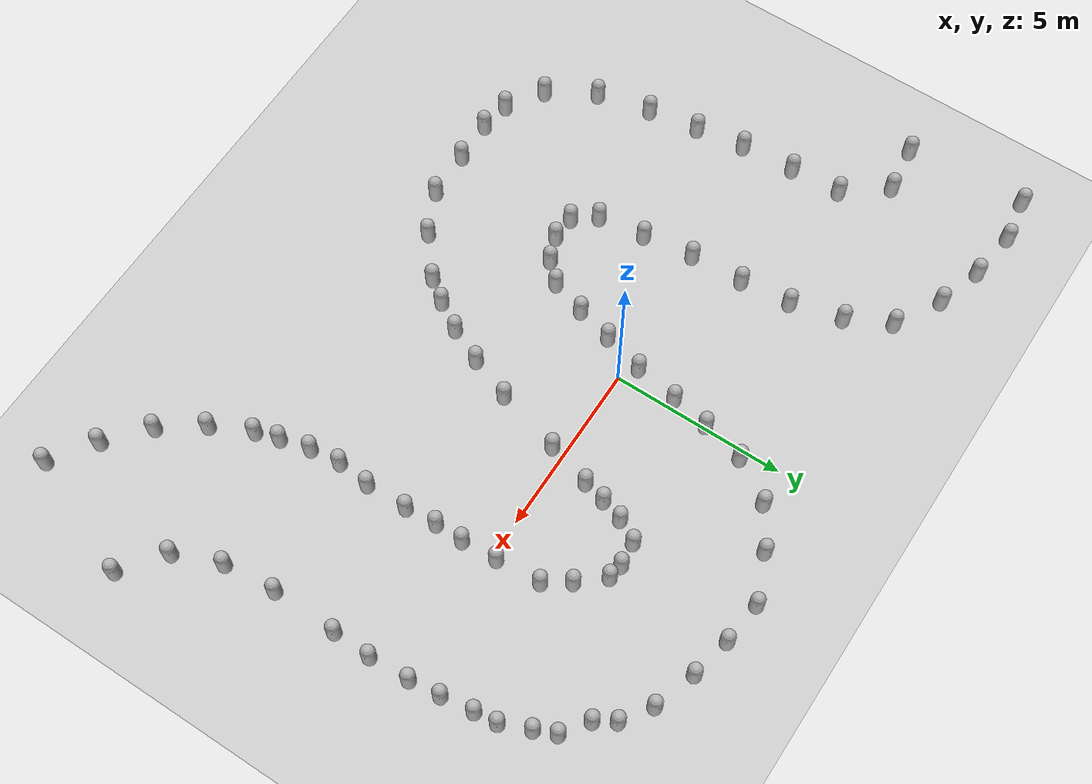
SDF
<sdf version='1.10'>
  <world name='empty'>
    <physics name='1ms' type='ignored'>
      <max_step_size>0.001</max_step_size>
      <real_time_factor>1</real_time_factor>
      <real_time_update_rate>1000</real_time_update_rate>
    </physics>
    <plugin name='gz::sim::systems::Physics' filename='gz-sim-physics-system'/>
    <plugin name='gz::sim::systems::UserCommands' filename='gz-sim-user-commands-system'/>
    <plugin name='gz::sim::systems::SceneBroadcaster' filename='gz-sim-scene-broadcaster-system'/>
    <plugin name='gz::sim::systems::Sensors' filename='gz-sim-sensors-system'>
      <render_engine>ogre2</render_engine>
    </plugin>
    <plugin name='gz::sim::systems::Contact' filename='gz-sim-contact-system'/>
    <gravity>0 0 -9.8000000000000007</gravity>
    <magnetic_field>5.5644999999999998e-06 2.2875799999999999e-05 -4.2388400000000002e-05</magnetic_field>
    <atmosphere type='adiabatic'/>
    <scene>
      <ambient>0.400000006 0.400000006 0.400000006 1</ambient>
      <background>0.699999988 0.699999988 0.699999988 1</background>
      <shadows>true</shadows>
    </scene>
    <model name='ground_plane'>
      <static>true</static>
      <link name='link'>
        <collision name='collision'>
          <geometry>
            <plane>
              <normal>0 0 1</normal>
              <size>100 100</size>
            </plane>
          </geometry>
          <surface>
            <friction>
              <ode/>
            </friction>
            <bounce/>
            <contact/>
          </surface>
        </collision>
        <visual name='visual'>
          <geometry>
            <plane>
              <normal>0 0 1</normal>
              <size>100 100</size>
            </plane>
          </geometry>
          <material>
            <ambient>0.800000012 0.800000012 0.800000012 1</ambient>
            <diffuse>0.800000012 0.800000012 0.800000012 1</diffuse>
            <specular>0.800000012 0.800000012 0.800000012 1</specular>
          </material>
        </visual>
        <pose>0 0 0 0 0 0</pose>
        <inertial>
          <pose>0 0 0 0 0 0</pose>
          <mass>1</mass>
          <inertia>
            <ixx>1</ixx>
            <ixy>0</ixy>
            <ixz>0</ixz>
            <iyy>1</iyy>
            <iyz>0</iyz>
            <izz>1</izz>
          </inertia>
        </inertial>
        <enable_wind>false</enable_wind>
      </link>
      <pose>0 0 0 0 0 0</pose>
      <self_collide>false</self_collide>
    </model>
    <model name='capsule'>
      <pose>5.0067120201532003 2.8950546282145462 0.49999999961384473 0 0 0</pose>
      <link name='capsule_link'>
        <inertial>
          <inertia>
            <ixx>0.074153999999999998</ixx>
            <ixy>0</ixy>
            <ixz>0</ixz>
            <iyy>0.074153999999999998</iyy>
            <iyz>0</iyz>
            <izz>0.018769000000000001</izz>
          </inertia>
          <mass>1</mass>
          <pose>0 0 0 0 0 0</pose>
        </inertial>
        <collision name='capsule_collision'>
          <geometry>
            <capsule>
              <radius>0.20000000000000001</radius>
              <length>0.59999999999999998</length>
            </capsule>
          </geometry>
          <surface>
            <friction>
              <ode/>
            </friction>
            <bounce/>
            <contact/>
          </surface>
        </collision>
        <visual name='capsule_visual'>
          <geometry>
            <capsule>
              <radius>0.20000000000000001</radius>
              <length>0.59999999999999998</length>
            </capsule>
          </geometry>
          <material>
            <ambient>0.300000012 0.300000012 0.300000012 1</ambient>
            <diffuse>0.699999988 0.699999988 0.699999988 1</diffuse>
            <specular>1 1 1 1</specular>
          </material>
        </visual>
        <pose>0 0 0 0 0 0</pose>
        <enable_wind>false</enable_wind>
      </link>
      <static>false</static>
      <self_collide>false</self_collide>
    </model>
    <model name='capsule_1'>
      <pose>6.0918446914484834 1.4883130985771231 0.49999999961384473 0 0 0</pose>
      <link name='capsule_link'>
        <inertial>
          <inertia>
            <ixx>0.074153999999999998</ixx>
            <ixy>0</ixy>
            <ixz>0</ixz>
            <iyy>0.074153999999999998</iyy>
            <iyz>0</iyz>
            <izz>0.018769000000000001</izz>
          </inertia>
          <mass>1</mass>
          <pose>0 0 0 0 0 0</pose>
        </inertial>
        <collision name='capsule_collision'>
          <geometry>
            <capsule>
              <radius>0.20000000000000001</radius>
              <length>0.59999999999999998</length>
            </capsule>
          </geometry>
          <surface>
            <friction>
              <ode/>
            </friction>
            <bounce/>
            <contact/>
          </surface>
        </collision>
        <visual name='capsule_visual'>
          <geometry>
            <capsule>
              <radius>0.20000000000000001</radius>
              <length>0.59999999999999998</length>
            </capsule>
          </geometry>
          <material>
            <ambient>0.300000012 0.300000012 0.300000012 1</ambient>
            <diffuse>0.699999988 0.699999988 0.699999988 1</diffuse>
            <specular>1 1 1 1</specular>
          </material>
        </visual>
        <pose>0 0 0 0 0 0</pose>
        <enable_wind>false</enable_wind>
      </link>
      <static>false</static>
      <self_collide>false</self_collide>
    </model>
    <model name='capsule_2'>
      <pose>6.2528500556945801 -0.81414926052093506 0.49999999980498194 0 0 0</pose>
      <link name='capsule_link'>
        <inertial>
          <inertia>
            <ixx>0.074153999999999998</ixx>
            <ixy>0</ixy>
            <ixz>0</ixz>
            <iyy>0.074153999999999998</iyy>
            <iyz>0</iyz>
            <izz>0.018769000000000001</izz>
          </inertia>
          <mass>1</mass>
          <pose>0 0 0 0 0 0</pose>
        </inertial>
        <collision name='capsule_collision'>
          <geometry>
            <capsule>
              <radius>0.20000000000000001</radius>
              <length>0.59999999999999998</length>
            </capsule>
          </geometry>
          <surface>
            <friction>
              <ode/>
            </friction>
            <bounce/>
            <contact/>
          </surface>
        </collision>
        <visual name='capsule_visual'>
          <geometry>
            <capsule>
              <radius>0.20000000000000001</radius>
              <length>0.59999999999999998</length>
            </capsule>
          </geometry>
          <material>
            <ambient>0.300000012 0.300000012 0.300000012 1</ambient>
            <diffuse>0.699999988 0.699999988 0.699999988 1</diffuse>
            <specular>1 1 1 1</specular>
          </material>
        </visual>
        <pose>0 0 0 0 0 0</pose>
        <enable_wind>false</enable_wind>
      </link>
      <static>false</static>
      <self_collide>false</self_collide>
    </model>
    <model name='capsule_3'>
      <pose>6.243919849395752 -1.6323399543762207 0.49999999980498194 0 0 0</pose>
      <link name='capsule_link'>
        <inertial>
          <inertia>
            <ixx>0.074153999999999998</ixx>
            <ixy>0</ixy>
            <ixz>0</ixz>
            <iyy>0.074153999999999998</iyy>
            <iyz>0</iyz>
            <izz>0.018769000000000001</izz>
          </inertia>
          <mass>1</mass>
          <pose>0 0 0 0 0 0</pose>
        </inertial>
        <collision name='capsule_collision'>
          <geometry>
            <capsule>
              <radius>0.20000000000000001</radius>
              <length>0.59999999999999998</length>
            </capsule>
          </geometry>
          <surface>
            <friction>
              <ode/>
            </friction>
            <bounce/>
            <contact/>
          </surface>
        </collision>
        <visual name='capsule_visual'>
          <geometry>
            <capsule>
              <radius>0.20000000000000001</radius>
              <length>0.59999999999999998</length>
            </capsule>
          </geometry>
          <material>
            <ambient>0.300000012 0.300000012 0.300000012 1</ambient>
            <diffuse>0.699999988 0.699999988 0.699999988 1</diffuse>
            <specular>1 1 1 1</specular>
          </material>
        </visual>
        <pose>0 0 0 0 0 0</pose>
        <enable_wind>false</enable_wind>
      </link>
      <static>false</static>
      <self_collide>false</self_collide>
    </model>
    <model name='capsule_4'>
      <pose>6.3168603929638234 -2.5392485538346374 0.49999999961384473 0 0 0</pose>
      <link name='capsule_link'>
        <inertial>
          <inertia>
            <ixx>0.074153999999999998</ixx>
            <ixy>0</ixy>
            <ixz>0</ixz>
            <iyy>0.074153999999999998</iyy>
            <iyz>0</iyz>
            <izz>0.018769000000000001</izz>
          </inertia>
          <mass>1</mass>
          <pose>0 0 0 0 0 0</pose>
        </inertial>
        <collision name='capsule_collision'>
          <geometry>
            <capsule>
              <radius>0.20000000000000001</radius>
              <length>0.59999999999999998</length>
            </capsule>
          </geometry>
          <surface>
            <friction>
              <ode/>
            </friction>
            <bounce/>
            <contact/>
          </surface>
        </collision>
        <visual name='capsule_visual'>
          <geometry>
            <capsule>
              <radius>0.20000000000000001</radius>
              <length>0.59999999999999998</length>
            </capsule>
          </geometry>
          <material>
            <ambient>0.300000012 0.300000012 0.300000012 1</ambient>
            <diffuse>0.699999988 0.699999988 0.699999988 1</diffuse>
            <specular>1 1 1 1</specular>
          </material>
        </visual>
        <pose>0 0 0 0 0 0</pose>
        <enable_wind>false</enable_wind>
      </link>
      <static>false</static>
      <self_collide>false</self_collide>
    </model>
    <model name='capsule_5'>
      <pose>6.3373173031823287 -3.7541128518168598 0.49999999961384473 0 0 0</pose>
      <link name='capsule_link'>
        <inertial>
          <inertia>
            <ixx>0.074153999999999998</ixx>
            <ixy>0</ixy>
            <ixz>0</ixz>
            <iyy>0.074153999999999998</iyy>
            <iyz>0</iyz>
            <izz>0.018769000000000001</izz>
          </inertia>
          <mass>1</mass>
          <pose>0 0 0 0 0 0</pose>
        </inertial>
        <collision name='capsule_collision'>
          <geometry>
            <capsule>
              <radius>0.20000000000000001</radius>
              <length>0.59999999999999998</length>
            </capsule>
          </geometry>
          <surface>
            <friction>
              <ode/>
            </friction>
            <bounce/>
            <contact/>
          </surface>
        </collision>
        <visual name='capsule_visual'>
          <geometry>
            <capsule>
              <radius>0.20000000000000001</radius>
              <length>0.59999999999999998</length>
            </capsule>
          </geometry>
          <material>
            <ambient>0.300000012 0.300000012 0.300000012 1</ambient>
            <diffuse>0.699999988 0.699999988 0.699999988 1</diffuse>
            <specular>1 1 1 1</specular>
          </material>
        </visual>
        <pose>0 0 0 0 0 0</pose>
        <enable_wind>false</enable_wind>
      </link>
      <static>false</static>
      <self_collide>false</self_collide>
    </model>
    <model name='capsule_6'>
      <pose>3.8893697356851402 2.892807902579547 0.49999999961384473 0 0 0</pose>
      <link name='capsule_link'>
        <inertial>
          <inertia>
            <ixx>0.074153999999999998</ixx>
            <ixy>0</ixy>
            <ixz>0</ixz>
            <iyy>0.074153999999999998</iyy>
            <iyz>0</iyz>
            <izz>0.018769000000000001</izz>
          </inertia>
          <mass>1</mass>
          <pose>0 0 0 0 0 0</pose>
        </inertial>
        <collision name='capsule_collision'>
          <geometry>
            <capsule>
              <radius>0.20000000000000001</radius>
              <length>0.59999999999999998</length>
            </capsule>
          </geometry>
          <surface>
            <friction>
              <ode/>
            </friction>
            <bounce/>
            <contact/>
          </surface>
        </collision>
        <visual name='capsule_visual'>
          <geometry>
            <capsule>
              <radius>0.20000000000000001</radius>
              <length>0.59999999999999998</length>
            </capsule>
          </geometry>
          <material>
            <ambient>0.300000012 0.300000012 0.300000012 1</ambient>
            <diffuse>0.699999988 0.699999988 0.699999988 1</diffuse>
            <specular>1 1 1 1</specular>
          </material>
        </visual>
        <pose>0 0 0 0 0 0</pose>
        <enable_wind>false</enable_wind>
      </link>
      <static>false</static>
      <self_collide>false</self_collide>
    </model>
    <model name='capsule_7'>
      <pose>3.3342243519569452 1.6304961430569558 0.49999999961384473 0 0 0</pose>
      <link name='capsule_link'>
        <inertial>
          <inertia>
            <ixx>0.074153999999999998</ixx>
            <ixy>0</ixy>
            <ixz>0</ixz>
            <iyy>0.074153999999999998</iyy>
            <iyz>0</iyz>
            <izz>0.018769000000000001</izz>
          </inertia>
          <mass>1</mass>
          <pose>0 0 0 0 0 0</pose>
        </inertial>
        <collision name='capsule_collision'>
          <geometry>
            <capsule>
              <radius>0.20000000000000001</radius>
              <length>0.59999999999999998</length>
            </capsule>
          </geometry>
          <surface>
            <friction>
              <ode/>
            </friction>
            <bounce/>
            <contact/>
          </surface>
        </collision>
        <visual name='capsule_visual'>
          <geometry>
            <capsule>
              <radius>0.20000000000000001</radius>
              <length>0.59999999999999998</length>
            </capsule>
          </geometry>
          <material>
            <ambient>0.300000012 0.300000012 0.300000012 1</ambient>
            <diffuse>0.699999988 0.699999988 0.699999988 1</diffuse>
            <specular>1 1 1 1</specular>
          </material>
        </visual>
        <pose>0 0 0 0 0 0</pose>
        <enable_wind>false</enable_wind>
      </link>
      <static>false</static>
      <self_collide>false</self_collide>
    </model>
    <model name='capsule_8'>
      <pose>3.1660099029541016 0.97390604019165039 0.49999999980498194 0 0 0</pose>
      <link name='capsule_link'>
        <inertial>
          <inertia>
            <ixx>0.074153999999999998</ixx>
            <ixy>0</ixy>
            <ixz>0</ixz>
            <iyy>0.074153999999999998</iyy>
            <iyz>0</iyz>
            <izz>0.018769000000000001</izz>
          </inertia>
          <mass>1</mass>
          <pose>0 0 0 0 0 0</pose>
        </inertial>
        <collision name='capsule_collision'>
          <geometry>
            <capsule>
              <radius>0.20000000000000001</radius>
              <length>0.59999999999999998</length>
            </capsule>
          </geometry>
          <surface>
            <friction>
              <ode/>
            </friction>
            <bounce/>
            <contact/>
          </surface>
        </collision>
        <visual name='capsule_visual'>
          <geometry>
            <capsule>
              <radius>0.20000000000000001</radius>
              <length>0.59999999999999998</length>
            </capsule>
          </geometry>
          <material>
            <ambient>0.300000012 0.300000012 0.300000012 1</ambient>
            <diffuse>0.699999988 0.699999988 0.699999988 1</diffuse>
            <specular>1 1 1 1</specular>
          </material>
        </visual>
        <pose>0 0 0 0 0 0</pose>
        <enable_wind>false</enable_wind>
      </link>
      <static>false</static>
      <self_collide>false</self_collide>
    </model>
    <model name='capsule_12'>
      <pose>9.9779636401044876 -4.026470124686111 0.49999999961384473 0 0 0</pose>
      <link name='capsule_link'>
        <inertial>
          <inertia>
            <ixx>0.074153999999999998</ixx>
            <ixy>0</ixy>
            <ixz>0</ixz>
            <iyy>0.074153999999999998</iyy>
            <iyz>0</iyz>
            <izz>0.018769000000000001</izz>
          </inertia>
          <mass>1</mass>
          <pose>0 0 0 0 0 0</pose>
        </inertial>
        <collision name='capsule_collision'>
          <geometry>
            <capsule>
              <radius>0.20000000000000001</radius>
              <length>0.59999999999999998</length>
            </capsule>
          </geometry>
          <surface>
            <friction>
              <ode/>
            </friction>
            <bounce/>
            <contact/>
          </surface>
        </collision>
        <visual name='capsule_visual'>
          <geometry>
            <capsule>
              <radius>0.20000000000000001</radius>
              <length>0.59999999999999998</length>
            </capsule>
          </geometry>
          <material>
            <ambient>0.300000012 0.300000012 0.300000012 1</ambient>
            <diffuse>0.699999988 0.699999988 0.699999988 1</diffuse>
            <specular>1 1 1 1</specular>
          </material>
        </visual>
        <pose>0 0 0 0 0 0</pose>
        <enable_wind>false</enable_wind>
      </link>
      <static>false</static>
      <self_collide>false</self_collide>
    </model>
    <model name='capsule_13'>
      <pose>10.02226374670887 -2.131533841577105 0.49999999961384473 0 0 0</pose>
      <link name='capsule_link'>
        <inertial>
          <inertia>
            <ixx>0.074153999999999998</ixx>
            <ixy>0</ixy>
            <ixz>0</ixz>
            <iyy>0.074153999999999998</iyy>
            <iyz>0</iyz>
            <izz>0.018769000000000001</izz>
          </inertia>
          <mass>1</mass>
          <pose>0 0 0 0 0 0</pose>
        </inertial>
        <collision name='capsule_collision'>
          <geometry>
            <capsule>
              <radius>0.20000000000000001</radius>
              <length>0.59999999999999998</length>
            </capsule>
          </geometry>
          <surface>
            <friction>
              <ode/>
            </friction>
            <bounce/>
            <contact/>
          </surface>
        </collision>
        <visual name='capsule_visual'>
          <geometry>
            <capsule>
              <radius>0.20000000000000001</radius>
              <length>0.59999999999999998</length>
            </capsule>
          </geometry>
          <material>
            <ambient>0.300000012 0.300000012 0.300000012 1</ambient>
            <diffuse>0.699999988 0.699999988 0.699999988 1</diffuse>
            <specular>1 1 1 1</specular>
          </material>
        </visual>
        <pose>0 0 0 0 0 0</pose>
        <enable_wind>false</enable_wind>
      </link>
      <static>false</static>
      <self_collide>false</self_collide>
    </model>
    <model name='capsule_14'>
      <pose>10.001105701659302 0.14882972912458661 0.49999999961384473 0 0 0</pose>
      <link name='capsule_link'>
        <inertial>
          <inertia>
            <ixx>0.074153999999999998</ixx>
            <ixy>0</ixy>
            <ixz>0</ixz>
            <iyy>0.074153999999999998</iyy>
            <iyz>0</iyz>
            <izz>0.018769000000000001</izz>
          </inertia>
          <mass>1</mass>
          <pose>0 0 0 0 0 0</pose>
        </inertial>
        <collision name='capsule_collision'>
          <geometry>
            <capsule>
              <radius>0.20000000000000001</radius>
              <length>0.59999999999999998</length>
            </capsule>
          </geometry>
          <surface>
            <friction>
              <ode/>
            </friction>
            <bounce/>
            <contact/>
          </surface>
        </collision>
        <visual name='capsule_visual'>
          <geometry>
            <capsule>
              <radius>0.20000000000000001</radius>
              <length>0.59999999999999998</length>
            </capsule>
          </geometry>
          <material>
            <ambient>0.300000012 0.300000012 0.300000012 1</ambient>
            <diffuse>0.699999988 0.699999988 0.699999988 1</diffuse>
            <specular>1 1 1 1</specular>
          </material>
        </visual>
        <pose>0 0 0 0 0 0</pose>
        <enable_wind>false</enable_wind>
      </link>
      <static>false</static>
      <self_collide>false</self_collide>
    </model>
    <model name='capsule_15'>
      <pose>9.7759025483170632 1.9615490699600033 0.49999999961384473 0 0 0</pose>
      <link name='capsule_link'>
        <inertial>
          <inertia>
            <ixx>0.074153999999999998</ixx>
            <ixy>0</ixy>
            <ixz>0</ixz>
            <iyy>0.074153999999999998</iyy>
            <iyz>0</iyz>
            <izz>0.018769000000000001</izz>
          </inertia>
          <mass>1</mass>
          <pose>0 0 0 0 0 0</pose>
        </inertial>
        <collision name='capsule_collision'>
          <geometry>
            <capsule>
              <radius>0.20000000000000001</radius>
              <length>0.59999999999999998</length>
            </capsule>
          </geometry>
          <surface>
            <friction>
              <ode/>
            </friction>
            <bounce/>
            <contact/>
          </surface>
        </collision>
        <visual name='capsule_visual'>
          <geometry>
            <capsule>
              <radius>0.20000000000000001</radius>
              <length>0.59999999999999998</length>
            </capsule>
          </geometry>
          <material>
            <ambient>0.300000012 0.300000012 0.300000012 1</ambient>
            <diffuse>0.699999988 0.699999988 0.699999988 1</diffuse>
            <specular>1 1 1 1</specular>
          </material>
        </visual>
        <pose>0 0 0 0 0 0</pose>
        <enable_wind>false</enable_wind>
      </link>
      <static>false</static>
      <self_collide>false</self_collide>
    </model>
    <model name='capsule_16'>
      <pose>9.362642894293721 3.4224772201174152 0.49999999961384473 0 0 0</pose>
      <link name='capsule_link'>
        <inertial>
          <inertia>
            <ixx>0.074153999999999998</ixx>
            <ixy>0</ixy>
            <ixz>0</ixz>
            <iyy>0.074153999999999998</iyy>
            <iyz>0</iyz>
            <izz>0.018769000000000001</izz>
          </inertia>
          <mass>1</mass>
          <pose>0 0 0 0 0 0</pose>
        </inertial>
        <collision name='capsule_collision'>
          <geometry>
            <capsule>
              <radius>0.20000000000000001</radius>
              <length>0.59999999999999998</length>
            </capsule>
          </geometry>
          <surface>
            <friction>
              <ode/>
            </friction>
            <bounce/>
            <contact/>
          </surface>
        </collision>
        <visual name='capsule_visual'>
          <geometry>
            <capsule>
              <radius>0.20000000000000001</radius>
              <length>0.59999999999999998</length>
            </capsule>
          </geometry>
          <material>
            <ambient>0.300000012 0.300000012 0.300000012 1</ambient>
            <diffuse>0.699999988 0.699999988 0.699999988 1</diffuse>
            <specular>1 1 1 1</specular>
          </material>
        </visual>
        <pose>0 0 0 0 0 0</pose>
        <enable_wind>false</enable_wind>
      </link>
      <static>false</static>
      <self_collide>false</self_collide>
    </model>
    <model name='capsule_17'>
      <pose>8.3764287410841902 4.5237605050009844 0.49999999961384473 0 0 0</pose>
      <link name='capsule_link'>
        <inertial>
          <inertia>
            <ixx>0.074153999999999998</ixx>
            <ixy>0</ixy>
            <ixz>0</ixz>
            <iyy>0.074153999999999998</iyy>
            <iyz>0</iyz>
            <izz>0.018769000000000001</izz>
          </inertia>
          <mass>1</mass>
          <pose>0 0 0 0 0 0</pose>
        </inertial>
        <collision name='capsule_collision'>
          <geometry>
            <capsule>
              <radius>0.20000000000000001</radius>
              <length>0.59999999999999998</length>
            </capsule>
          </geometry>
          <surface>
            <friction>
              <ode/>
            </friction>
            <bounce/>
            <contact/>
          </surface>
        </collision>
        <visual name='capsule_visual'>
          <geometry>
            <capsule>
              <radius>0.20000000000000001</radius>
              <length>0.59999999999999998</length>
            </capsule>
          </geometry>
          <material>
            <ambient>0.300000012 0.300000012 0.300000012 1</ambient>
            <diffuse>0.699999988 0.699999988 0.699999988 1</diffuse>
            <specular>1 1 1 1</specular>
          </material>
        </visual>
        <pose>0 0 0 0 0 0</pose>
        <enable_wind>false</enable_wind>
      </link>
      <static>false</static>
      <self_collide>false</self_collide>
    </model>
    <model name='capsule_18'>
      <pose>7.2165150779495999 5.6198774742734647 0.49999999961384473 0 0 0</pose>
      <link name='capsule_link'>
        <inertial>
          <inertia>
            <ixx>0.074153999999999998</ixx>
            <ixy>0</ixy>
            <ixz>0</ixz>
            <iyy>0.074153999999999998</iyy>
            <iyz>0</iyz>
            <izz>0.018769000000000001</izz>
          </inertia>
          <mass>1</mass>
          <pose>0 0 0 0 0 0</pose>
        </inertial>
        <collision name='capsule_collision'>
          <geometry>
            <capsule>
              <radius>0.20000000000000001</radius>
              <length>0.59999999999999998</length>
            </capsule>
          </geometry>
          <surface>
            <friction>
              <ode/>
            </friction>
            <bounce/>
            <contact/>
          </surface>
        </collision>
        <visual name='capsule_visual'>
          <geometry>
            <capsule>
              <radius>0.20000000000000001</radius>
              <length>0.59999999999999998</length>
            </capsule>
          </geometry>
          <material>
            <ambient>0.300000012 0.300000012 0.300000012 1</ambient>
            <diffuse>0.699999988 0.699999988 0.699999988 1</diffuse>
            <specular>1 1 1 1</specular>
          </material>
        </visual>
        <pose>0 0 0 0 0 0</pose>
        <enable_wind>false</enable_wind>
      </link>
      <static>false</static>
      <self_collide>false</self_collide>
    </model>
    <model name='capsule_19'>
      <pose>5.9928646797740672 6.0196110714190141 0.49999999961384473 0 0 0</pose>
      <link name='capsule_link'>
        <inertial>
          <inertia>
            <ixx>0.074153999999999998</ixx>
            <ixy>0</ixy>
            <ixz>0</ixz>
            <iyy>0.074153999999999998</iyy>
            <iyz>0</iyz>
            <izz>0.018769000000000001</izz>
          </inertia>
          <mass>1</mass>
          <pose>0 0 0 0 0 0</pose>
        </inertial>
        <collision name='capsule_collision'>
          <geometry>
            <capsule>
              <radius>0.20000000000000001</radius>
              <length>0.59999999999999998</length>
            </capsule>
          </geometry>
          <surface>
            <friction>
              <ode/>
            </friction>
            <bounce/>
            <contact/>
          </surface>
        </collision>
        <visual name='capsule_visual'>
          <geometry>
            <capsule>
              <radius>0.20000000000000001</radius>
              <length>0.59999999999999998</length>
            </capsule>
          </geometry>
          <material>
            <ambient>0.300000012 0.300000012 0.300000012 1</ambient>
            <diffuse>0.699999988 0.699999988 0.699999988 1</diffuse>
            <specular>1 1 1 1</specular>
          </material>
        </visual>
        <pose>0 0 0 0 0 0</pose>
        <enable_wind>false</enable_wind>
      </link>
      <static>false</static>
      <self_collide>false</self_collide>
    </model>
    <model name='capsule_20'>
      <pose>4.8129751771360949 6.2641878366718666 0.49999999961384473 0 0 0</pose>
      <link name='capsule_link'>
        <inertial>
          <inertia>
            <ixx>0.074153999999999998</ixx>
            <ixy>0</ixy>
            <ixz>0</ixz>
            <iyy>0.074153999999999998</iyy>
            <iyz>0</iyz>
            <izz>0.018769000000000001</izz>
          </inertia>
          <mass>1</mass>
          <pose>0 0 0 0 0 0</pose>
        </inertial>
        <collision name='capsule_collision'>
          <geometry>
            <capsule>
              <radius>0.20000000000000001</radius>
              <length>0.59999999999999998</length>
            </capsule>
          </geometry>
          <surface>
            <friction>
              <ode/>
            </friction>
            <bounce/>
            <contact/>
          </surface>
        </collision>
        <visual name='capsule_visual'>
          <geometry>
            <capsule>
              <radius>0.20000000000000001</radius>
              <length>0.59999999999999998</length>
            </capsule>
          </geometry>
          <material>
            <ambient>0.300000012 0.300000012 0.300000012 1</ambient>
            <diffuse>0.699999988 0.699999988 0.699999988 1</diffuse>
            <specular>1 1 1 1</specular>
          </material>
        </visual>
        <pose>0 0 0 0 0 0</pose>
        <enable_wind>false</enable_wind>
      </link>
      <static>false</static>
      <self_collide>false</self_collide>
    </model>
    <model name='capsule_21'>
      <pose>3.5784910898476814 6.3930733778430691 0.49999999961384473 0 0 0</pose>
      <link name='capsule_link'>
        <inertial>
          <inertia>
            <ixx>0.074153999999999998</ixx>
            <ixy>0</ixy>
            <ixz>0</ixz>
            <iyy>0.074153999999999998</iyy>
            <iyz>0</iyz>
            <izz>0.018769000000000001</izz>
          </inertia>
          <mass>1</mass>
          <pose>0 0 0 0 0 0</pose>
        </inertial>
        <collision name='capsule_collision'>
          <geometry>
            <capsule>
              <radius>0.20000000000000001</radius>
              <length>0.59999999999999998</length>
            </capsule>
          </geometry>
          <surface>
            <friction>
              <ode/>
            </friction>
            <bounce/>
            <contact/>
          </surface>
        </collision>
        <visual name='capsule_visual'>
          <geometry>
            <capsule>
              <radius>0.20000000000000001</radius>
              <length>0.59999999999999998</length>
            </capsule>
          </geometry>
          <material>
            <ambient>0.300000012 0.300000012 0.300000012 1</ambient>
            <diffuse>0.699999988 0.699999988 0.699999988 1</diffuse>
            <specular>1 1 1 1</specular>
          </material>
        </visual>
        <pose>0 0 0 0 0 0</pose>
        <enable_wind>false</enable_wind>
      </link>
      <static>false</static>
      <self_collide>false</self_collide>
    </model>
    <model name='capsule_22'>
      <pose>2.2410211586859279 5.8455925256962518 0.49999999961384473 0 0 0</pose>
      <link name='capsule_link'>
        <inertial>
          <inertia>
            <ixx>0.074153999999999998</ixx>
            <ixy>0</ixy>
            <ixz>0</ixz>
            <iyy>0.074153999999999998</iyy>
            <iyz>0</iyz>
            <izz>0.018769000000000001</izz>
          </inertia>
          <mass>1</mass>
          <pose>0 0 0 0 0 0</pose>
        </inertial>
        <collision name='capsule_collision'>
          <geometry>
            <capsule>
              <radius>0.20000000000000001</radius>
              <length>0.59999999999999998</length>
            </capsule>
          </geometry>
          <surface>
            <friction>
              <ode/>
            </friction>
            <bounce/>
            <contact/>
          </surface>
        </collision>
        <visual name='capsule_visual'>
          <geometry>
            <capsule>
              <radius>0.20000000000000001</radius>
              <length>0.59999999999999998</length>
            </capsule>
          </geometry>
          <material>
            <ambient>0.300000012 0.300000012 0.300000012 1</ambient>
            <diffuse>0.699999988 0.699999988 0.699999988 1</diffuse>
            <specular>1 1 1 1</specular>
          </material>
        </visual>
        <pose>0 0 0 0 0 0</pose>
        <enable_wind>false</enable_wind>
      </link>
      <static>false</static>
      <self_collide>false</self_collide>
    </model>
    <model name='capsule_23'>
      <pose>1.1205332928616789 5.148689651645503 0.49999999961384473 0 0 0</pose>
      <link name='capsule_link'>
        <inertial>
          <inertia>
            <ixx>0.074153999999999998</ixx>
            <ixy>0</ixy>
            <ixz>0</ixz>
            <iyy>0.074153999999999998</iyy>
            <iyz>0</iyz>
            <izz>0.018769000000000001</izz>
          </inertia>
          <mass>1</mass>
          <pose>0 0 0 0 0 0</pose>
        </inertial>
        <collision name='capsule_collision'>
          <geometry>
            <capsule>
              <radius>0.20000000000000001</radius>
              <length>0.59999999999999998</length>
            </capsule>
          </geometry>
          <surface>
            <friction>
              <ode/>
            </friction>
            <bounce/>
            <contact/>
          </surface>
        </collision>
        <visual name='capsule_visual'>
          <geometry>
            <capsule>
              <radius>0.20000000000000001</radius>
              <length>0.59999999999999998</length>
            </capsule>
          </geometry>
          <material>
            <ambient>0.300000012 0.300000012 0.300000012 1</ambient>
            <diffuse>0.699999988 0.699999988 0.699999988 1</diffuse>
            <specular>1 1 1 1</specular>
          </material>
        </visual>
        <pose>0 0 0 0 0 0</pose>
        <enable_wind>false</enable_wind>
      </link>
      <static>false</static>
      <self_collide>false</self_collide>
    </model>
    <model name='capsule_24'>
      <pose>0.36715474724769592 3.9862101078033447 0.49999999980498194 0 0 0</pose>
      <link name='capsule_link'>
        <inertial>
          <inertia>
            <ixx>0.074153999999999998</ixx>
            <ixy>0</ixy>
            <ixz>0</ixz>
            <iyy>0.074153999999999998</iyy>
            <iyz>0</iyz>
            <izz>0.018769000000000001</izz>
          </inertia>
          <mass>1</mass>
          <pose>0 0 0 0 0 0</pose>
        </inertial>
        <collision name='capsule_collision'>
          <geometry>
            <capsule>
              <radius>0.20000000000000001</radius>
              <length>0.59999999999999998</length>
            </capsule>
          </geometry>
          <surface>
            <friction>
              <ode/>
            </friction>
            <bounce/>
            <contact/>
          </surface>
        </collision>
        <visual name='capsule_visual'>
          <geometry>
            <capsule>
              <radius>0.20000000000000001</radius>
              <length>0.59999999999999998</length>
            </capsule>
          </geometry>
          <material>
            <ambient>0.300000012 0.300000012 0.300000012 1</ambient>
            <diffuse>0.699999988 0.699999988 0.699999988 1</diffuse>
            <specular>1 1 1 1</specular>
          </material>
        </visual>
        <pose>0 0 0 0 0 0</pose>
        <enable_wind>false</enable_wind>
      </link>
      <static>false</static>
      <self_collide>false</self_collide>
    </model>
    <model name='capsule_25'>
      <pose>0.054870724678039551 2.7515799999237061 0.49999999980498194 0 0 0</pose>
      <link name='capsule_link'>
        <inertial>
          <inertia>
            <ixx>0.074153999999999998</ixx>
            <ixy>0</ixy>
            <ixz>0</ixz>
            <iyy>0.074153999999999998</iyy>
            <iyz>0</iyz>
            <izz>0.018769000000000001</izz>
          </inertia>
          <mass>1</mass>
          <pose>0 0 0 0 0 0</pose>
        </inertial>
        <collision name='capsule_collision'>
          <geometry>
            <capsule>
              <radius>0.20000000000000001</radius>
              <length>0.59999999999999998</length>
            </capsule>
          </geometry>
          <surface>
            <friction>
              <ode/>
            </friction>
            <bounce/>
            <contact/>
          </surface>
        </collision>
        <visual name='capsule_visual'>
          <geometry>
            <capsule>
              <radius>0.20000000000000001</radius>
              <length>0.59999999999999998</length>
            </capsule>
          </geometry>
          <material>
            <ambient>0.300000012 0.300000012 0.300000012 1</ambient>
            <diffuse>0.699999988 0.699999988 0.699999988 1</diffuse>
            <specular>1 1 1 1</specular>
          </material>
        </visual>
        <pose>0 0 0 0 0 0</pose>
        <enable_wind>false</enable_wind>
      </link>
      <static>false</static>
      <self_collide>false</self_collide>
    </model>
    <model name='capsule_26'>
      <pose>-0.14112371206283569 1.6486799716949463 0.49999999980498194 0 0 0</pose>
      <link name='capsule_link'>
        <inertial>
          <inertia>
            <ixx>0.074153999999999998</ixx>
            <ixy>0</ixy>
            <ixz>0</ixz>
            <iyy>0.074153999999999998</iyy>
            <iyz>0</iyz>
            <izz>0.018769000000000001</izz>
          </inertia>
          <mass>1</mass>
          <pose>0 0 0 0 0 0</pose>
        </inertial>
        <collision name='capsule_collision'>
          <geometry>
            <capsule>
              <radius>0.20000000000000001</radius>
              <length>0.59999999999999998</length>
            </capsule>
          </geometry>
          <surface>
            <friction>
              <ode/>
            </friction>
            <bounce/>
            <contact/>
          </surface>
        </collision>
        <visual name='capsule_visual'>
          <geometry>
            <capsule>
              <radius>0.20000000000000001</radius>
              <length>0.59999999999999998</length>
            </capsule>
          </geometry>
          <material>
            <ambient>0.300000012 0.300000012 0.300000012 1</ambient>
            <diffuse>0.699999988 0.699999988 0.699999988 1</diffuse>
            <specular>1 1 1 1</specular>
          </material>
        </visual>
        <pose>0 0 0 0 0 0</pose>
        <enable_wind>false</enable_wind>
      </link>
      <static>false</static>
      <self_collide>false</self_collide>
    </model>
    <model name='capsule_33'>
      <pose>-3.7359690886875785 -3.0206758947746262 0.49999999961384473 0 0 0</pose>
      <link name='capsule_link'>
        <inertial>
          <inertia>
            <ixx>0.074153999999999998</ixx>
            <ixy>0</ixy>
            <ixz>0</ixz>
            <iyy>0.074153999999999998</iyy>
            <iyz>0</iyz>
            <izz>0.018769000000000001</izz>
          </inertia>
          <mass>1</mass>
          <pose>0 0 0 0 0 0</pose>
        </inertial>
        <collision name='capsule_collision'>
          <geometry>
            <capsule>
              <radius>0.20000000000000001</radius>
              <length>0.59999999999999998</length>
            </capsule>
          </geometry>
          <surface>
            <friction>
              <ode/>
            </friction>
            <bounce/>
            <contact/>
          </surface>
        </collision>
        <visual name='capsule_visual'>
          <geometry>
            <capsule>
              <radius>0.20000000000000001</radius>
              <length>0.59999999999999998</length>
            </capsule>
          </geometry>
          <material>
            <ambient>0.300000012 0.300000012 0.300000012 1</ambient>
            <diffuse>0.699999988 0.699999988 0.699999988 1</diffuse>
            <specular>1 1 1 1</specular>
          </material>
        </visual>
        <pose>0 0 0 0 0 0</pose>
        <enable_wind>false</enable_wind>
      </link>
      <static>false</static>
      <self_collide>false</self_collide>
    </model>
    <model name='capsule_34'>
      <pose>-3.9136007308902969 -1.6616885756400075 0.49999999961384473 0 0 0</pose>
      <link name='capsule_link'>
        <inertial>
          <inertia>
            <ixx>0.074153999999999998</ixx>
            <ixy>0</ixy>
            <ixz>0</ixz>
            <iyy>0.074153999999999998</iyy>
            <iyz>0</iyz>
            <izz>0.018769000000000001</izz>
          </inertia>
          <mass>1</mass>
          <pose>0 0 0 0 0 0</pose>
        </inertial>
        <collision name='capsule_collision'>
          <geometry>
            <capsule>
              <radius>0.20000000000000001</radius>
              <length>0.59999999999999998</length>
            </capsule>
          </geometry>
          <surface>
            <friction>
              <ode/>
            </friction>
            <bounce/>
            <contact/>
          </surface>
        </collision>
        <visual name='capsule_visual'>
          <geometry>
            <capsule>
              <radius>0.20000000000000001</radius>
              <length>0.59999999999999998</length>
            </capsule>
          </geometry>
          <material>
            <ambient>0.300000012 0.300000012 0.300000012 1</ambient>
            <diffuse>0.699999988 0.699999988 0.699999988 1</diffuse>
            <specular>1 1 1 1</specular>
          </material>
        </visual>
        <pose>0 0 0 0 0 0</pose>
        <enable_wind>false</enable_wind>
      </link>
      <static>false</static>
      <self_collide>false</self_collide>
    </model>
    <model name='capsule_35'>
      <pose>-4.111023931562845 -0.20660173922643699 0.49999999961384473 0 0 0</pose>
      <link name='capsule_link'>
        <inertial>
          <inertia>
            <ixx>0.074153999999999998</ixx>
            <ixy>0</ixy>
            <ixz>0</ixz>
            <iyy>0.074153999999999998</iyy>
            <iyz>0</iyz>
            <izz>0.018769000000000001</izz>
          </inertia>
          <mass>1</mass>
          <pose>0 0 0 0 0 0</pose>
        </inertial>
        <collision name='capsule_collision'>
          <geometry>
            <capsule>
              <radius>0.20000000000000001</radius>
              <length>0.59999999999999998</length>
            </capsule>
          </geometry>
          <surface>
            <friction>
              <ode/>
            </friction>
            <bounce/>
            <contact/>
          </surface>
        </collision>
        <visual name='capsule_visual'>
          <geometry>
            <capsule>
              <radius>0.20000000000000001</radius>
              <length>0.59999999999999998</length>
            </capsule>
          </geometry>
          <material>
            <ambient>0.300000012 0.300000012 0.300000012 1</ambient>
            <diffuse>0.699999988 0.699999988 0.699999988 1</diffuse>
            <specular>1 1 1 1</specular>
          </material>
        </visual>
        <pose>0 0 0 0 0 0</pose>
        <enable_wind>false</enable_wind>
      </link>
      <static>false</static>
      <self_collide>false</self_collide>
    </model>
    <model name='capsule_36'>
      <pose>-4.1761549505182636 1.3268821165121976 0.49999999961384473 0 0 0</pose>
      <link name='capsule_link'>
        <inertial>
          <inertia>
            <ixx>0.074153999999999998</ixx>
            <ixy>0</ixy>
            <ixz>0</ixz>
            <iyy>0.074153999999999998</iyy>
            <iyz>0</iyz>
            <izz>0.018769000000000001</izz>
          </inertia>
          <mass>1</mass>
          <pose>0 0 0 0 0 0</pose>
        </inertial>
        <collision name='capsule_collision'>
          <geometry>
            <capsule>
              <radius>0.20000000000000001</radius>
              <length>0.59999999999999998</length>
            </capsule>
          </geometry>
          <surface>
            <friction>
              <ode/>
            </friction>
            <bounce/>
            <contact/>
          </surface>
        </collision>
        <visual name='capsule_visual'>
          <geometry>
            <capsule>
              <radius>0.20000000000000001</radius>
              <length>0.59999999999999998</length>
            </capsule>
          </geometry>
          <material>
            <ambient>0.300000012 0.300000012 0.300000012 1</ambient>
            <diffuse>0.699999988 0.699999988 0.699999988 1</diffuse>
            <specular>1 1 1 1</specular>
          </material>
        </visual>
        <pose>0 0 0 0 0 0</pose>
        <enable_wind>false</enable_wind>
      </link>
      <static>false</static>
      <self_collide>false</self_collide>
    </model>
    <model name='capsule_37'>
      <pose>-4.3167518290005216 2.7823156699431575 0.49999999961384473 0 0 0</pose>
      <link name='capsule_link'>
        <inertial>
          <inertia>
            <ixx>0.074153999999999998</ixx>
            <ixy>0</ixy>
            <ixz>0</ixz>
            <iyy>0.074153999999999998</iyy>
            <iyz>0</iyz>
            <izz>0.018769000000000001</izz>
          </inertia>
          <mass>1</mass>
          <pose>0 0 0 0 0 0</pose>
        </inertial>
        <collision name='capsule_collision'>
          <geometry>
            <capsule>
              <radius>0.20000000000000001</radius>
              <length>0.59999999999999998</length>
            </capsule>
          </geometry>
          <surface>
            <friction>
              <ode/>
            </friction>
            <bounce/>
            <contact/>
          </surface>
        </collision>
        <visual name='capsule_visual'>
          <geometry>
            <capsule>
              <radius>0.20000000000000001</radius>
              <length>0.59999999999999998</length>
            </capsule>
          </geometry>
          <material>
            <ambient>0.300000012 0.300000012 0.300000012 1</ambient>
            <diffuse>0.699999988 0.699999988 0.699999988 1</diffuse>
            <specular>1 1 1 1</specular>
          </material>
        </visual>
        <pose>0 0 0 0 0 0</pose>
        <enable_wind>false</enable_wind>
      </link>
      <static>false</static>
      <self_collide>false</self_collide>
    </model>
    <model name='capsule_44'>
      <pose>-5.3499398231506348 -7.2536706924438477 0.499999999902001 0 0 0</pose>
      <link name='capsule_link'>
        <inertial>
          <inertia>
            <ixx>0.074153999999999998</ixx>
            <ixy>0</ixy>
            <ixz>0</ixz>
            <iyy>0.074153999999999998</iyy>
            <iyz>0</iyz>
            <izz>0.018769000000000001</izz>
          </inertia>
          <mass>1</mass>
          <pose>0 0 0 0 0 0</pose>
        </inertial>
        <collision name='capsule_collision'>
          <geometry>
            <capsule>
              <radius>0.20000000000000001</radius>
              <length>0.59999999999999998</length>
            </capsule>
          </geometry>
          <surface>
            <friction>
              <ode/>
            </friction>
            <bounce/>
            <contact/>
          </surface>
        </collision>
        <visual name='capsule_visual'>
          <geometry>
            <capsule>
              <radius>0.20000000000000001</radius>
              <length>0.59999999999999998</length>
            </capsule>
          </geometry>
          <material>
            <ambient>0.300000012 0.300000012 0.300000012 1</ambient>
            <diffuse>0.699999988 0.699999988 0.699999988 1</diffuse>
            <specular>1 1 1 1</specular>
          </material>
        </visual>
        <pose>0 0 0 0 0 0</pose>
        <enable_wind>false</enable_wind>
      </link>
      <static>false</static>
      <self_collide>false</self_collide>
    </model>
    <model name='capsule_45'>
      <pose>-6.3835868845907884 -6.5850210009494328 0.49999999961384473 0 0 0</pose>
      <link name='capsule_link'>
        <inertial>
          <inertia>
            <ixx>0.074153999999999998</ixx>
            <ixy>0</ixy>
            <ixz>0</ixz>
            <iyy>0.074153999999999998</iyy>
            <iyz>0</iyz>
            <izz>0.018769000000000001</izz>
          </inertia>
          <mass>1</mass>
          <pose>0 0 0 0 0 0</pose>
        </inertial>
        <collision name='capsule_collision'>
          <geometry>
            <capsule>
              <radius>0.20000000000000001</radius>
              <length>0.59999999999999998</length>
            </capsule>
          </geometry>
          <surface>
            <friction>
              <ode/>
            </friction>
            <bounce/>
            <contact/>
          </surface>
        </collision>
        <visual name='capsule_visual'>
          <geometry>
            <capsule>
              <radius>0.20000000000000001</radius>
              <length>0.59999999999999998</length>
            </capsule>
          </geometry>
          <material>
            <ambient>0.300000012 0.300000012 0.300000012 1</ambient>
            <diffuse>0.699999988 0.699999988 0.699999988 1</diffuse>
            <specular>1 1 1 1</specular>
          </material>
        </visual>
        <pose>0 0 0 0 0 0</pose>
        <enable_wind>false</enable_wind>
      </link>
      <static>false</static>
      <self_collide>false</self_collide>
    </model>
    <model name='capsule_46'>
      <pose>-7.151202088566734 -5.24470062890338 0.49999999961384473 0 0 0</pose>
      <link name='capsule_link'>
        <inertial>
          <inertia>
            <ixx>0.074153999999999998</ixx>
            <ixy>0</ixy>
            <ixz>0</ixz>
            <iyy>0.074153999999999998</iyy>
            <iyz>0</iyz>
            <izz>0.018769000000000001</izz>
          </inertia>
          <mass>1</mass>
          <pose>0 0 0 0 0 0</pose>
        </inertial>
        <collision name='capsule_collision'>
          <geometry>
            <capsule>
              <radius>0.20000000000000001</radius>
              <length>0.59999999999999998</length>
            </capsule>
          </geometry>
          <surface>
            <friction>
              <ode/>
            </friction>
            <bounce/>
            <contact/>
          </surface>
        </collision>
        <visual name='capsule_visual'>
          <geometry>
            <capsule>
              <radius>0.20000000000000001</radius>
              <length>0.59999999999999998</length>
            </capsule>
          </geometry>
          <material>
            <ambient>0.300000012 0.300000012 0.300000012 1</ambient>
            <diffuse>0.699999988 0.699999988 0.699999988 1</diffuse>
            <specular>1 1 1 1</specular>
          </material>
        </visual>
        <pose>0 0 0 0 0 0</pose>
        <enable_wind>false</enable_wind>
      </link>
      <static>false</static>
      <self_collide>false</self_collide>
    </model>
    <model name='capsule_47'>
      <pose>-7.5092744102022229 -3.7053056780459031 0.49999999961384473 0 0 0</pose>
      <link name='capsule_link'>
        <inertial>
          <inertia>
            <ixx>0.074153999999999998</ixx>
            <ixy>0</ixy>
            <ixz>0</ixz>
            <iyy>0.074153999999999998</iyy>
            <iyz>0</iyz>
            <izz>0.018769000000000001</izz>
          </inertia>
          <mass>1</mass>
          <pose>0 0 0 0 0 0</pose>
        </inertial>
        <collision name='capsule_collision'>
          <geometry>
            <capsule>
              <radius>0.20000000000000001</radius>
              <length>0.59999999999999998</length>
            </capsule>
          </geometry>
          <surface>
            <friction>
              <ode/>
            </friction>
            <bounce/>
            <contact/>
          </surface>
        </collision>
        <visual name='capsule_visual'>
          <geometry>
            <capsule>
              <radius>0.20000000000000001</radius>
              <length>0.59999999999999998</length>
            </capsule>
          </geometry>
          <material>
            <ambient>0.300000012 0.300000012 0.300000012 1</ambient>
            <diffuse>0.699999988 0.699999988 0.699999988 1</diffuse>
            <specular>1 1 1 1</specular>
          </material>
        </visual>
        <pose>0 0 0 0 0 0</pose>
        <enable_wind>false</enable_wind>
      </link>
      <static>false</static>
      <self_collide>false</self_collide>
    </model>
    <model name='capsule_48'>
      <pose>-7.7253568550493883 -2.2453464417871847 0.49999999961384473 0 0 0</pose>
      <link name='capsule_link'>
        <inertial>
          <inertia>
            <ixx>0.074153999999999998</ixx>
            <ixy>0</ixy>
            <ixz>0</ixz>
            <iyy>0.074153999999999998</iyy>
            <iyz>0</iyz>
            <izz>0.018769000000000001</izz>
          </inertia>
          <mass>1</mass>
          <pose>0 0 0 0 0 0</pose>
        </inertial>
        <collision name='capsule_collision'>
          <geometry>
            <capsule>
              <radius>0.20000000000000001</radius>
              <length>0.59999999999999998</length>
            </capsule>
          </geometry>
          <surface>
            <friction>
              <ode/>
            </friction>
            <bounce/>
            <contact/>
          </surface>
        </collision>
        <visual name='capsule_visual'>
          <geometry>
            <capsule>
              <radius>0.20000000000000001</radius>
              <length>0.59999999999999998</length>
            </capsule>
          </geometry>
          <material>
            <ambient>0.300000012 0.300000012 0.300000012 1</ambient>
            <diffuse>0.699999988 0.699999988 0.699999988 1</diffuse>
            <specular>1 1 1 1</specular>
          </material>
        </visual>
        <pose>0 0 0 0 0 0</pose>
        <enable_wind>false</enable_wind>
      </link>
      <static>false</static>
      <self_collide>false</self_collide>
    </model>
    <model name='capsule_49'>
      <pose>-7.9444842494851269 -0.84214427424519833 0.49999999961384473 0 0 0</pose>
      <link name='capsule_link'>
        <inertial>
          <inertia>
            <ixx>0.074153999999999998</ixx>
            <ixy>0</ixy>
            <ixz>0</ixz>
            <iyy>0.074153999999999998</iyy>
            <iyz>0</iyz>
            <izz>0.018769000000000001</izz>
          </inertia>
          <mass>1</mass>
          <pose>0 0 0 0 0 0</pose>
        </inertial>
        <collision name='capsule_collision'>
          <geometry>
            <capsule>
              <radius>0.20000000000000001</radius>
              <length>0.59999999999999998</length>
            </capsule>
          </geometry>
          <surface>
            <friction>
              <ode/>
            </friction>
            <bounce/>
            <contact/>
          </surface>
        </collision>
        <visual name='capsule_visual'>
          <geometry>
            <capsule>
              <radius>0.20000000000000001</radius>
              <length>0.59999999999999998</length>
            </capsule>
          </geometry>
          <material>
            <ambient>0.300000012 0.300000012 0.300000012 1</ambient>
            <diffuse>0.699999988 0.699999988 0.699999988 1</diffuse>
            <specular>1 1 1 1</specular>
          </material>
        </visual>
        <pose>0 0 0 0 0 0</pose>
        <enable_wind>false</enable_wind>
      </link>
      <static>false</static>
      <self_collide>false</self_collide>
    </model>
    <model name='capsule_50'>
      <pose>-8.0543399608816379 0.70126440235399068 0.49999999961384473 0 0 0</pose>
      <link name='capsule_link'>
        <inertial>
          <inertia>
            <ixx>0.074153999999999998</ixx>
            <ixy>0</ixy>
            <ixz>0</ixz>
            <iyy>0.074153999999999998</iyy>
            <iyz>0</iyz>
            <izz>0.018769000000000001</izz>
          </inertia>
          <mass>1</mass>
          <pose>0 0 0 0 0 0</pose>
        </inertial>
        <collision name='capsule_collision'>
          <geometry>
            <capsule>
              <radius>0.20000000000000001</radius>
              <length>0.59999999999999998</length>
            </capsule>
          </geometry>
          <surface>
            <friction>
              <ode/>
            </friction>
            <bounce/>
            <contact/>
          </surface>
        </collision>
        <visual name='capsule_visual'>
          <geometry>
            <capsule>
              <radius>0.20000000000000001</radius>
              <length>0.59999999999999998</length>
            </capsule>
          </geometry>
          <material>
            <ambient>0.300000012 0.300000012 0.300000012 1</ambient>
            <diffuse>0.699999988 0.699999988 0.699999988 1</diffuse>
            <specular>1 1 1 1</specular>
          </material>
        </visual>
        <pose>0 0 0 0 0 0</pose>
        <enable_wind>false</enable_wind>
      </link>
      <static>false</static>
      <self_collide>false</self_collide>
    </model>
    <model name='capsule_51'>
      <pose>-8.133668301421551 2.1621473446861521 0.49999999961384473 0 0 0</pose>
      <link name='capsule_link'>
        <inertial>
          <inertia>
            <ixx>0.074153999999999998</ixx>
            <ixy>0</ixy>
            <ixz>0</ixz>
            <iyy>0.074153999999999998</iyy>
            <iyz>0</iyz>
            <izz>0.018769000000000001</izz>
          </inertia>
          <mass>1</mass>
          <pose>0 0 0 0 0 0</pose>
        </inertial>
        <collision name='capsule_collision'>
          <geometry>
            <capsule>
              <radius>0.20000000000000001</radius>
              <length>0.59999999999999998</length>
            </capsule>
          </geometry>
          <surface>
            <friction>
              <ode/>
            </friction>
            <bounce/>
            <contact/>
          </surface>
        </collision>
        <visual name='capsule_visual'>
          <geometry>
            <capsule>
              <radius>0.20000000000000001</radius>
              <length>0.59999999999999998</length>
            </capsule>
          </geometry>
          <material>
            <ambient>0.300000012 0.300000012 0.300000012 1</ambient>
            <diffuse>0.699999988 0.699999988 0.699999988 1</diffuse>
            <specular>1 1 1 1</specular>
          </material>
        </visual>
        <pose>0 0 0 0 0 0</pose>
        <enable_wind>false</enable_wind>
      </link>
      <static>false</static>
      <self_collide>false</self_collide>
    </model>
    <model name='capsule_52'>
      <pose>-9.0635232539598647 3.3592041852973571 0.49999999961384473 0 0 0</pose>
      <link name='capsule_link'>
        <inertial>
          <inertia>
            <ixx>0.074153999999999998</ixx>
            <ixy>0</ixy>
            <ixz>0</ixz>
            <iyy>0.074153999999999998</iyy>
            <iyz>0</iyz>
            <izz>0.018769000000000001</izz>
          </inertia>
          <mass>1</mass>
          <pose>0 0 0 0 0 0</pose>
        </inertial>
        <collision name='capsule_collision'>
          <geometry>
            <capsule>
              <radius>0.20000000000000001</radius>
              <length>0.59999999999999998</length>
            </capsule>
          </geometry>
          <surface>
            <friction>
              <ode/>
            </friction>
            <bounce/>
            <contact/>
          </surface>
        </collision>
        <visual name='capsule_visual'>
          <geometry>
            <capsule>
              <radius>0.20000000000000001</radius>
              <length>0.59999999999999998</length>
            </capsule>
          </geometry>
          <material>
            <ambient>0.300000012 0.300000012 0.300000012 1</ambient>
            <diffuse>0.699999988 0.699999988 0.699999988 1</diffuse>
            <specular>1 1 1 1</specular>
          </material>
        </visual>
        <pose>0 0 0 0 0 0</pose>
        <enable_wind>false</enable_wind>
      </link>
      <static>false</static>
      <self_collide>false</self_collide>
    </model>
    <model name='capsule_53'>
      <pose>-10.406988290166627 3.1960569281330056 0.49999999961384473 0 0 0</pose>
      <link name='capsule_link'>
        <inertial>
          <inertia>
            <ixx>0.074153999999999998</ixx>
            <ixy>0</ixy>
            <ixz>0</ixz>
            <iyy>0.074153999999999998</iyy>
            <iyz>0</iyz>
            <izz>0.018769000000000001</izz>
          </inertia>
          <mass>1</mass>
          <pose>0 0 0 0 0 0</pose>
        </inertial>
        <collision name='capsule_collision'>
          <geometry>
            <capsule>
              <radius>0.20000000000000001</radius>
              <length>0.59999999999999998</length>
            </capsule>
          </geometry>
          <surface>
            <friction>
              <ode/>
            </friction>
            <bounce/>
            <contact/>
          </surface>
        </collision>
        <visual name='capsule_visual'>
          <geometry>
            <capsule>
              <radius>0.20000000000000001</radius>
              <length>0.59999999999999998</length>
            </capsule>
          </geometry>
          <material>
            <ambient>0.300000012 0.300000012 0.300000012 1</ambient>
            <diffuse>0.699999988 0.699999988 0.699999988 1</diffuse>
            <specular>1 1 1 1</specular>
          </material>
        </visual>
        <pose>0 0 0 0 0 0</pose>
        <enable_wind>false</enable_wind>
      </link>
      <static>false</static>
      <self_collide>false</self_collide>
    </model>
    <model name='capsule_54'>
      <pose>-4.6987325271913631 4.2416568152282537 0.49999999961384473 0 0 0</pose>
      <link name='capsule_link'>
        <inertial>
          <inertia>
            <ixx>0.074153999999999998</ixx>
            <ixy>0</ixy>
            <ixz>0</ixz>
            <iyy>0.074153999999999998</iyy>
            <iyz>0</iyz>
            <izz>0.018769000000000001</izz>
          </inertia>
          <mass>1</mass>
          <pose>0 0 0 0 0 0</pose>
        </inertial>
        <collision name='capsule_collision'>
          <geometry>
            <capsule>
              <radius>0.20000000000000001</radius>
              <length>0.59999999999999998</length>
            </capsule>
          </geometry>
          <surface>
            <friction>
              <ode/>
            </friction>
            <bounce/>
            <contact/>
          </surface>
        </collision>
        <visual name='capsule_visual'>
          <geometry>
            <capsule>
              <radius>0.20000000000000001</radius>
              <length>0.59999999999999998</length>
            </capsule>
          </geometry>
          <material>
            <ambient>0.300000012 0.300000012 0.300000012 1</ambient>
            <diffuse>0.699999988 0.699999988 0.699999988 1</diffuse>
            <specular>1 1 1 1</specular>
          </material>
        </visual>
        <pose>0 0 0 0 0 0</pose>
        <enable_wind>false</enable_wind>
      </link>
      <static>false</static>
      <self_collide>false</self_collide>
    </model>
    <model name='capsule_55'>
      <pose>-5.3272928059358069 5.4728657916276644 0.49999999961384473 0 0 0</pose>
      <link name='capsule_link'>
        <inertial>
          <inertia>
            <ixx>0.074153999999999998</ixx>
            <ixy>0</ixy>
            <ixz>0</ixz>
            <iyy>0.074153999999999998</iyy>
            <iyz>0</iyz>
            <izz>0.018769000000000001</izz>
          </inertia>
          <mass>1</mass>
          <pose>0 0 0 0 0 0</pose>
        </inertial>
        <collision name='capsule_collision'>
          <geometry>
            <capsule>
              <radius>0.20000000000000001</radius>
              <length>0.59999999999999998</length>
            </capsule>
          </geometry>
          <surface>
            <friction>
              <ode/>
            </friction>
            <bounce/>
            <contact/>
          </surface>
        </collision>
        <visual name='capsule_visual'>
          <geometry>
            <capsule>
              <radius>0.20000000000000001</radius>
              <length>0.59999999999999998</length>
            </capsule>
          </geometry>
          <material>
            <ambient>0.300000012 0.300000012 0.300000012 1</ambient>
            <diffuse>0.699999988 0.699999988 0.699999988 1</diffuse>
            <specular>1 1 1 1</specular>
          </material>
        </visual>
        <pose>0 0 0 0 0 0</pose>
        <enable_wind>false</enable_wind>
      </link>
      <static>false</static>
      <self_collide>false</self_collide>
    </model>
    <model name='capsule_56'>
      <pose>-6.6353722595975215 6.219936998346852 0.49999999961384473 0 0 0</pose>
      <link name='capsule_link'>
        <inertial>
          <inertia>
            <ixx>0.074153999999999998</ixx>
            <ixy>0</ixy>
            <ixz>0</ixz>
            <iyy>0.074153999999999998</iyy>
            <iyz>0</iyz>
            <izz>0.018769000000000001</izz>
          </inertia>
          <mass>1</mass>
          <pose>0 0 0 0 0 0</pose>
        </inertial>
        <collision name='capsule_collision'>
          <geometry>
            <capsule>
              <radius>0.20000000000000001</radius>
              <length>0.59999999999999998</length>
            </capsule>
          </geometry>
          <surface>
            <friction>
              <ode/>
            </friction>
            <bounce/>
            <contact/>
          </surface>
        </collision>
        <visual name='capsule_visual'>
          <geometry>
            <capsule>
              <radius>0.20000000000000001</radius>
              <length>0.59999999999999998</length>
            </capsule>
          </geometry>
          <material>
            <ambient>0.300000012 0.300000012 0.300000012 1</ambient>
            <diffuse>0.699999988 0.699999988 0.699999988 1</diffuse>
            <specular>1 1 1 1</specular>
          </material>
        </visual>
        <pose>0 0 0 0 0 0</pose>
        <enable_wind>false</enable_wind>
      </link>
      <static>false</static>
      <self_collide>false</self_collide>
    </model>
    <model name='capsule_57'>
      <pose>-7.9635487807413075 6.63476376183496 0.49999999961384473 0 0 0</pose>
      <link name='capsule_link'>
        <inertial>
          <inertia>
            <ixx>0.074153999999999998</ixx>
            <ixy>0</ixy>
            <ixz>0</ixz>
            <iyy>0.074153999999999998</iyy>
            <iyz>0</iyz>
            <izz>0.018769000000000001</izz>
          </inertia>
          <mass>1</mass>
          <pose>0 0 0 0 0 0</pose>
        </inertial>
        <collision name='capsule_collision'>
          <geometry>
            <capsule>
              <radius>0.20000000000000001</radius>
              <length>0.59999999999999998</length>
            </capsule>
          </geometry>
          <surface>
            <friction>
              <ode/>
            </friction>
            <bounce/>
            <contact/>
          </surface>
        </collision>
        <visual name='capsule_visual'>
          <geometry>
            <capsule>
              <radius>0.20000000000000001</radius>
              <length>0.59999999999999998</length>
            </capsule>
          </geometry>
          <material>
            <ambient>0.300000012 0.300000012 0.300000012 1</ambient>
            <diffuse>0.699999988 0.699999988 0.699999988 1</diffuse>
            <specular>1 1 1 1</specular>
          </material>
        </visual>
        <pose>0 0 0 0 0 0</pose>
        <enable_wind>false</enable_wind>
      </link>
      <static>false</static>
      <self_collide>false</self_collide>
    </model>
    <model name='capsule_58'>
      <pose>-9.3985387470740029 6.8278514270354265 0.49999999961384473 0 0 0</pose>
      <link name='capsule_link'>
        <inertial>
          <inertia>
            <ixx>0.074153999999999998</ixx>
            <ixy>0</ixy>
            <ixz>0</ixz>
            <iyy>0.074153999999999998</iyy>
            <iyz>0</iyz>
            <izz>0.018769000000000001</izz>
          </inertia>
          <mass>1</mass>
          <pose>0 0 0 0 0 0</pose>
        </inertial>
        <collision name='capsule_collision'>
          <geometry>
            <capsule>
              <radius>0.20000000000000001</radius>
              <length>0.59999999999999998</length>
            </capsule>
          </geometry>
          <surface>
            <friction>
              <ode/>
            </friction>
            <bounce/>
            <contact/>
          </surface>
        </collision>
        <visual name='capsule_visual'>
          <geometry>
            <capsule>
              <radius>0.20000000000000001</radius>
              <length>0.59999999999999998</length>
            </capsule>
          </geometry>
          <material>
            <ambient>0.300000012 0.300000012 0.300000012 1</ambient>
            <diffuse>0.699999988 0.699999988 0.699999988 1</diffuse>
            <specular>1 1 1 1</specular>
          </material>
        </visual>
        <pose>0 0 0 0 0 0</pose>
        <enable_wind>false</enable_wind>
      </link>
      <static>false</static>
      <self_collide>false</self_collide>
    </model>
    <model name='capsule_59'>
      <pose>-10.630884424231226 6.6370643973520558 0.49999999961384473 0 0 0</pose>
      <link name='capsule_link'>
        <inertial>
          <inertia>
            <ixx>0.074153999999999998</ixx>
            <ixy>0</ixy>
            <ixz>0</ixz>
            <iyy>0.074153999999999998</iyy>
            <iyz>0</iyz>
            <izz>0.018769000000000001</izz>
          </inertia>
          <mass>1</mass>
          <pose>0 0 0 0 0 0</pose>
        </inertial>
        <collision name='capsule_collision'>
          <geometry>
            <capsule>
              <radius>0.20000000000000001</radius>
              <length>0.59999999999999998</length>
            </capsule>
          </geometry>
          <surface>
            <friction>
              <ode/>
            </friction>
            <bounce/>
            <contact/>
          </surface>
        </collision>
        <visual name='capsule_visual'>
          <geometry>
            <capsule>
              <radius>0.20000000000000001</radius>
              <length>0.59999999999999998</length>
            </capsule>
          </geometry>
          <material>
            <ambient>0.300000012 0.300000012 0.300000012 1</ambient>
            <diffuse>0.699999988 0.699999988 0.699999988 1</diffuse>
            <specular>1 1 1 1</specular>
          </material>
        </visual>
        <pose>0 0 0 0 0 0</pose>
        <enable_wind>false</enable_wind>
      </link>
      <static>false</static>
      <self_collide>false</self_collide>
    </model>
    <model name='capsule_60'>
      <pose>6.3314919959247762 -5.590667238932638 0.49999999961384473 0 0 0</pose>
      <link name='capsule_link'>
        <inertial>
          <inertia>
            <ixx>0.074153999999999998</ixx>
            <ixy>0</ixy>
            <ixz>0</ixz>
            <iyy>0.074153999999999998</iyy>
            <iyz>0</iyz>
            <izz>0.018769000000000001</izz>
          </inertia>
          <mass>1</mass>
          <pose>0 0 0 0 0 0</pose>
        </inertial>
        <collision name='capsule_collision'>
          <geometry>
            <capsule>
              <radius>0.20000000000000001</radius>
              <length>0.59999999999999998</length>
            </capsule>
          </geometry>
          <surface>
            <friction>
              <ode/>
            </friction>
            <bounce/>
            <contact/>
          </surface>
        </collision>
        <visual name='capsule_visual'>
          <geometry>
            <capsule>
              <radius>0.20000000000000001</radius>
              <length>0.59999999999999998</length>
            </capsule>
          </geometry>
          <material>
            <ambient>0.300000012 0.300000012 0.300000012 1</ambient>
            <diffuse>0.699999988 0.699999988 0.699999988 1</diffuse>
            <specular>1 1 1 1</specular>
          </material>
        </visual>
        <pose>0 0 0 0 0 0</pose>
        <enable_wind>false</enable_wind>
      </link>
      <static>false</static>
      <self_collide>false</self_collide>
    </model>
    <model name='capsule_61'>
      <pose>10.11741301168127 -5.5325644207378035 0.49999999961384473 0 0 0</pose>
      <link name='capsule_link'>
        <inertial>
          <inertia>
            <ixx>0.074153999999999998</ixx>
            <ixy>0</ixy>
            <ixz>0</ixz>
            <iyy>0.074153999999999998</iyy>
            <iyz>0</iyz>
            <izz>0.018769000000000001</izz>
          </inertia>
          <mass>1</mass>
          <pose>0 0 0 0 0 0</pose>
        </inertial>
        <collision name='capsule_collision'>
          <geometry>
            <capsule>
              <radius>0.20000000000000001</radius>
              <length>0.59999999999999998</length>
            </capsule>
          </geometry>
          <surface>
            <friction>
              <ode/>
            </friction>
            <bounce/>
            <contact/>
          </surface>
        </collision>
        <visual name='capsule_visual'>
          <geometry>
            <capsule>
              <radius>0.20000000000000001</radius>
              <length>0.59999999999999998</length>
            </capsule>
          </geometry>
          <material>
            <ambient>0.300000012 0.300000012 0.300000012 1</ambient>
            <diffuse>0.699999988 0.699999988 0.699999988 1</diffuse>
            <specular>1 1 1 1</specular>
          </material>
        </visual>
        <pose>0 0 0 0 0 0</pose>
        <enable_wind>false</enable_wind>
      </link>
      <static>false</static>
      <self_collide>false</self_collide>
    </model>
    <model name='capsule_62'>
      <pose>10.644863435152994 -6.8593919314908725 0.49999999961384473 0 0 0</pose>
      <link name='capsule_link'>
        <inertial>
          <inertia>
            <ixx>0.074153999999999998</ixx>
            <ixy>0</ixy>
            <ixz>0</ixz>
            <iyy>0.074153999999999998</iyy>
            <iyz>0</iyz>
            <izz>0.018769000000000001</izz>
          </inertia>
          <mass>1</mass>
          <pose>0 0 0 0 0 0</pose>
        </inertial>
        <collision name='capsule_collision'>
          <geometry>
            <capsule>
              <radius>0.20000000000000001</radius>
              <length>0.59999999999999998</length>
            </capsule>
          </geometry>
          <surface>
            <friction>
              <ode/>
            </friction>
            <bounce/>
            <contact/>
          </surface>
        </collision>
        <visual name='capsule_visual'>
          <geometry>
            <capsule>
              <radius>0.20000000000000001</radius>
              <length>0.59999999999999998</length>
            </capsule>
          </geometry>
          <material>
            <ambient>0.300000012 0.300000012 0.300000012 1</ambient>
            <diffuse>0.699999988 0.699999988 0.699999988 1</diffuse>
            <specular>1 1 1 1</specular>
          </material>
        </visual>
        <pose>0 0 0 0 0 0</pose>
        <enable_wind>false</enable_wind>
      </link>
      <static>false</static>
      <self_collide>false</self_collide>
    </model>
    <model name='capsule_63'>
      <pose>6.7479515674650221 -7.1104412985510148 0.49999999961384473 0 0 0</pose>
      <link name='capsule_link'>
        <inertial>
          <inertia>
            <ixx>0.074153999999999998</ixx>
            <ixy>0</ixy>
            <ixz>0</ixz>
            <iyy>0.074153999999999998</iyy>
            <iyz>0</iyz>
            <izz>0.018769000000000001</izz>
          </inertia>
          <mass>1</mass>
          <pose>0 0 0 0 0 0</pose>
        </inertial>
        <collision name='capsule_collision'>
          <geometry>
            <capsule>
              <radius>0.20000000000000001</radius>
              <length>0.59999999999999998</length>
            </capsule>
          </geometry>
          <surface>
            <friction>
              <ode/>
            </friction>
            <bounce/>
            <contact/>
          </surface>
        </collision>
        <visual name='capsule_visual'>
          <geometry>
            <capsule>
              <radius>0.20000000000000001</radius>
              <length>0.59999999999999998</length>
            </capsule>
          </geometry>
          <material>
            <ambient>0.300000012 0.300000012 0.300000012 1</ambient>
            <diffuse>0.699999988 0.699999988 0.699999988 1</diffuse>
            <specular>1 1 1 1</specular>
          </material>
        </visual>
        <pose>0 0 0 0 0 0</pose>
        <enable_wind>false</enable_wind>
      </link>
      <static>false</static>
      <self_collide>false</self_collide>
    </model>
    <model name='capsule_64'>
      <pose>7.2963945963359151 -8.240016975941133 0.49999999961384473 0 0 0</pose>
      <link name='capsule_link'>
        <inertial>
          <inertia>
            <ixx>0.074153999999999998</ixx>
            <ixy>0</ixy>
            <ixz>0</ixz>
            <iyy>0.074153999999999998</iyy>
            <iyz>0</iyz>
            <izz>0.018769000000000001</izz>
          </inertia>
          <mass>1</mass>
          <pose>0 0 0 0 0 0</pose>
        </inertial>
        <collision name='capsule_collision'>
          <geometry>
            <capsule>
              <radius>0.20000000000000001</radius>
              <length>0.59999999999999998</length>
            </capsule>
          </geometry>
          <surface>
            <friction>
              <ode/>
            </friction>
            <bounce/>
            <contact/>
          </surface>
        </collision>
        <visual name='capsule_visual'>
          <geometry>
            <capsule>
              <radius>0.20000000000000001</radius>
              <length>0.59999999999999998</length>
            </capsule>
          </geometry>
          <material>
            <ambient>0.300000012 0.300000012 0.300000012 1</ambient>
            <diffuse>0.699999988 0.699999988 0.699999988 1</diffuse>
            <specular>1 1 1 1</specular>
          </material>
        </visual>
        <pose>0 0 0 0 0 0</pose>
        <enable_wind>false</enable_wind>
      </link>
      <static>false</static>
      <self_collide>false</self_collide>
    </model>
    <model name='capsule_65'>
      <pose>8.1228659711914588 -9.3929300923327759 0.49999999961384473 0 0 0</pose>
      <link name='capsule_link'>
        <inertial>
          <inertia>
            <ixx>0.074153999999999998</ixx>
            <ixy>0</ixy>
            <ixz>0</ixz>
            <iyy>0.074153999999999998</iyy>
            <iyz>0</iyz>
            <izz>0.018769000000000001</izz>
          </inertia>
          <mass>1</mass>
          <pose>0 0 0 0 0 0</pose>
        </inertial>
        <collision name='capsule_collision'>
          <geometry>
            <capsule>
              <radius>0.20000000000000001</radius>
              <length>0.59999999999999998</length>
            </capsule>
          </geometry>
          <surface>
            <friction>
              <ode/>
            </friction>
            <bounce/>
            <contact/>
          </surface>
        </collision>
        <visual name='capsule_visual'>
          <geometry>
            <capsule>
              <radius>0.20000000000000001</radius>
              <length>0.59999999999999998</length>
            </capsule>
          </geometry>
          <material>
            <ambient>0.300000012 0.300000012 0.300000012 1</ambient>
            <diffuse>0.699999988 0.699999988 0.699999988 1</diffuse>
            <specular>1 1 1 1</specular>
          </material>
        </visual>
        <pose>0 0 0 0 0 0</pose>
        <enable_wind>false</enable_wind>
      </link>
      <static>false</static>
      <self_collide>false</self_collide>
    </model>
    <model name='capsule_66'>
      <pose>9.2258935134949915 -10.349220092928032 0.49999999961384473 0 0 0</pose>
      <link name='capsule_link'>
        <inertial>
          <inertia>
            <ixx>0.074153999999999998</ixx>
            <ixy>0</ixy>
            <ixz>0</ixz>
            <iyy>0.074153999999999998</iyy>
            <iyz>0</iyz>
            <izz>0.018769000000000001</izz>
          </inertia>
          <mass>1</mass>
          <pose>0 0 0 0 0 0</pose>
        </inertial>
        <collision name='capsule_collision'>
          <geometry>
            <capsule>
              <radius>0.20000000000000001</radius>
              <length>0.59999999999999998</length>
            </capsule>
          </geometry>
          <surface>
            <friction>
              <ode/>
            </friction>
            <bounce/>
            <contact/>
          </surface>
        </collision>
        <visual name='capsule_visual'>
          <geometry>
            <capsule>
              <radius>0.20000000000000001</radius>
              <length>0.59999999999999998</length>
            </capsule>
          </geometry>
          <material>
            <ambient>0.300000012 0.300000012 0.300000012 1</ambient>
            <diffuse>0.699999988 0.699999988 0.699999988 1</diffuse>
            <specular>1 1 1 1</specular>
          </material>
        </visual>
        <pose>0 0 0 0 0 0</pose>
        <enable_wind>false</enable_wind>
      </link>
      <static>false</static>
      <self_collide>false</self_collide>
    </model>
    <model name='capsule_67'>
      <pose>10.440839469349417 -11.195331756799842 0.49999999961384473 0 0 0</pose>
      <link name='capsule_link'>
        <inertial>
          <inertia>
            <ixx>0.074153999999999998</ixx>
            <ixy>0</ixy>
            <ixz>0</ixz>
            <iyy>0.074153999999999998</iyy>
            <iyz>0</iyz>
            <izz>0.018769000000000001</izz>
          </inertia>
          <mass>1</mass>
          <pose>0 0 0 0 0 0</pose>
        </inertial>
        <collision name='capsule_collision'>
          <geometry>
            <capsule>
              <radius>0.20000000000000001</radius>
              <length>0.59999999999999998</length>
            </capsule>
          </geometry>
          <surface>
            <friction>
              <ode/>
            </friction>
            <bounce/>
            <contact/>
          </surface>
        </collision>
        <visual name='capsule_visual'>
          <geometry>
            <capsule>
              <radius>0.20000000000000001</radius>
              <length>0.59999999999999998</length>
            </capsule>
          </geometry>
          <material>
            <ambient>0.300000012 0.300000012 0.300000012 1</ambient>
            <diffuse>0.699999988 0.699999988 0.699999988 1</diffuse>
            <specular>1 1 1 1</specular>
          </material>
        </visual>
        <pose>0 0 0 0 0 0</pose>
        <enable_wind>false</enable_wind>
      </link>
      <static>false</static>
      <self_collide>false</self_collide>
    </model>
    <model name='capsule_68'>
      <pose>11.81976249762786 -7.7683201869391816 0.49999999961384473 0 0 0</pose>
      <link name='capsule_link'>
        <inertial>
          <inertia>
            <ixx>0.074153999999999998</ixx>
            <ixy>0</ixy>
            <ixz>0</ixz>
            <iyy>0.074153999999999998</iyy>
            <iyz>0</iyz>
            <izz>0.018769000000000001</izz>
          </inertia>
          <mass>1</mass>
          <pose>0 0 0 0 0 0</pose>
        </inertial>
        <collision name='capsule_collision'>
          <geometry>
            <capsule>
              <radius>0.20000000000000001</radius>
              <length>0.59999999999999998</length>
            </capsule>
          </geometry>
          <surface>
            <friction>
              <ode/>
            </friction>
            <bounce/>
            <contact/>
          </surface>
        </collision>
        <visual name='capsule_visual'>
          <geometry>
            <capsule>
              <radius>0.20000000000000001</radius>
              <length>0.59999999999999998</length>
            </capsule>
          </geometry>
          <material>
            <ambient>0.300000012 0.300000012 0.300000012 1</ambient>
            <diffuse>0.699999988 0.699999988 0.699999988 1</diffuse>
            <specular>1 1 1 1</specular>
          </material>
        </visual>
        <pose>0 0 0 0 0 0</pose>
        <enable_wind>false</enable_wind>
      </link>
      <static>false</static>
      <self_collide>false</self_collide>
    </model>
    <model name='capsule_27'>
      <pose>-0.38106293636721733 0.38151102855183938 0.49999999961384473 0 0 0</pose>
      <link name='capsule_link'>
        <inertial>
          <inertia>
            <ixx>0.074153999999999998</ixx>
            <ixy>0</ixy>
            <ixz>0</ixz>
            <iyy>0.074153999999999998</iyy>
            <iyz>0</iyz>
            <izz>0.018769000000000001</izz>
          </inertia>
          <mass>1</mass>
          <pose>0 0 0 0 0 0</pose>
        </inertial>
        <collision name='capsule_collision'>
          <geometry>
            <capsule>
              <radius>0.20000000000000001</radius>
              <length>0.59999999999999998</length>
            </capsule>
          </geometry>
          <surface>
            <friction>
              <ode/>
            </friction>
            <bounce/>
            <contact/>
          </surface>
        </collision>
        <visual name='capsule_visual'>
          <geometry>
            <capsule>
              <radius>0.20000000000000001</radius>
              <length>0.59999999999999998</length>
            </capsule>
          </geometry>
          <material>
            <ambient>0.300000012 0.300000012 0.300000012 1</ambient>
            <diffuse>0.699999988 0.699999988 0.699999988 1</diffuse>
            <specular>1 1 1 1</specular>
          </material>
        </visual>
        <pose>0 0 0 0 0 0</pose>
        <enable_wind>false</enable_wind>
      </link>
      <static>false</static>
      <self_collide>false</self_collide>
    </model>
    <model name='capsule_38_8'>
      <pose>5.6302345674589258 2.1911713154369741 0.49999999970893311 0 0 0</pose>
      <link name='capsule_link'>
        <inertial>
          <inertia>
            <ixx>0.074153999999999998</ixx>
            <ixy>0</ixy>
            <ixz>0</ixz>
            <iyy>0.074153999999999998</iyy>
            <iyz>0</iyz>
            <izz>0.018769000000000001</izz>
          </inertia>
          <mass>1</mass>
          <pose>0 0 0 0 0 0</pose>
        </inertial>
        <collision name='capsule_collision'>
          <geometry>
            <capsule>
              <radius>0.20000000000000001</radius>
              <length>0.59999999999999998</length>
            </capsule>
          </geometry>
          <surface>
            <friction>
              <ode/>
            </friction>
            <bounce/>
            <contact/>
          </surface>
        </collision>
        <visual name='capsule_visual'>
          <geometry>
            <capsule>
              <radius>0.20000000000000001</radius>
              <length>0.59999999999999998</length>
            </capsule>
          </geometry>
          <material>
            <ambient>0.300000012 0.300000012 0.300000012 1</ambient>
            <diffuse>0.699999988 0.699999988 0.699999988 1</diffuse>
            <specular>1 1 1 1</specular>
          </material>
        </visual>
        <pose>0 0 0 0 0 0</pose>
        <enable_wind>false</enable_wind>
      </link>
      <static>false</static>
      <self_collide>false</self_collide>
    </model>
    <model name='capsule_38_9'>
      <pose>6.1898999214172363 0.2068728506565094 0.49999999980498194 0 0 0</pose>
      <link name='capsule_link'>
        <inertial>
          <inertia>
            <ixx>0.074153999999999998</ixx>
            <ixy>0</ixy>
            <ixz>0</ixz>
            <iyy>0.074153999999999998</iyy>
            <iyz>0</iyz>
            <izz>0.018769000000000001</izz>
          </inertia>
          <mass>1</mass>
          <pose>0 0 0 0 0 0</pose>
        </inertial>
        <collision name='capsule_collision'>
          <geometry>
            <capsule>
              <radius>0.20000000000000001</radius>
              <length>0.59999999999999998</length>
            </capsule>
          </geometry>
          <surface>
            <friction>
              <ode/>
            </friction>
            <bounce/>
            <contact/>
          </surface>
        </collision>
        <visual name='capsule_visual'>
          <geometry>
            <capsule>
              <radius>0.20000000000000001</radius>
              <length>0.59999999999999998</length>
            </capsule>
          </geometry>
          <material>
            <ambient>0.300000012 0.300000012 0.300000012 1</ambient>
            <diffuse>0.699999988 0.699999988 0.699999988 1</diffuse>
            <specular>1 1 1 1</specular>
          </material>
        </visual>
        <pose>0 0 0 0 0 0</pose>
        <enable_wind>false</enable_wind>
      </link>
      <static>false</static>
      <self_collide>false</self_collide>
    </model>
    <model name='capsule_38_10'>
      <pose>10.057748138936249 -1.0164653281757277 0.49999999970893311 0 0 0</pose>
      <link name='capsule_link'>
        <inertial>
          <inertia>
            <ixx>0.074153999999999998</ixx>
            <ixy>0</ixy>
            <ixz>0</ixz>
            <iyy>0.074153999999999998</iyy>
            <iyz>0</iyz>
            <izz>0.018769000000000001</izz>
          </inertia>
          <mass>1</mass>
          <pose>0 0 0 0 0 0</pose>
        </inertial>
        <collision name='capsule_collision'>
          <geometry>
            <capsule>
              <radius>0.20000000000000001</radius>
              <length>0.59999999999999998</length>
            </capsule>
          </geometry>
          <surface>
            <friction>
              <ode/>
            </friction>
            <bounce/>
            <contact/>
          </surface>
        </collision>
        <visual name='capsule_visual'>
          <geometry>
            <capsule>
              <radius>0.20000000000000001</radius>
              <length>0.59999999999999998</length>
            </capsule>
          </geometry>
          <material>
            <ambient>0.300000012 0.300000012 0.300000012 1</ambient>
            <diffuse>0.699999988 0.699999988 0.699999988 1</diffuse>
            <specular>1 1 1 1</specular>
          </material>
        </visual>
        <pose>0 0 0 0 0 0</pose>
        <enable_wind>false</enable_wind>
      </link>
      <static>false</static>
      <self_collide>false</self_collide>
    </model>
    <model name='capsule_38_11'>
      <pose>6.2315090613109092 -4.7152401779612045 0.49999999970893311 0 0 0</pose>
      <link name='capsule_link'>
        <inertial>
          <inertia>
            <ixx>0.074153999999999998</ixx>
            <ixy>0</ixy>
            <ixz>0</ixz>
            <iyy>0.074153999999999998</iyy>
            <iyz>0</iyz>
            <izz>0.018769000000000001</izz>
          </inertia>
          <mass>1</mass>
          <pose>0 0 0 0 0 0</pose>
        </inertial>
        <collision name='capsule_collision'>
          <geometry>
            <capsule>
              <radius>0.20000000000000001</radius>
              <length>0.59999999999999998</length>
            </capsule>
          </geometry>
          <surface>
            <friction>
              <ode/>
            </friction>
            <bounce/>
            <contact/>
          </surface>
        </collision>
        <visual name='capsule_visual'>
          <geometry>
            <capsule>
              <radius>0.20000000000000001</radius>
              <length>0.59999999999999998</length>
            </capsule>
          </geometry>
          <material>
            <ambient>0.300000012 0.300000012 0.300000012 1</ambient>
            <diffuse>0.699999988 0.699999988 0.699999988 1</diffuse>
            <specular>1 1 1 1</specular>
          </material>
        </visual>
        <pose>0 0 0 0 0 0</pose>
        <enable_wind>false</enable_wind>
      </link>
      <static>false</static>
      <self_collide>false</self_collide>
    </model>
    <model name='capsule_38_12'>
      <pose>6.5513221531392958 -6.4425884682645211 0.49999999970893311 0 0 0</pose>
      <link name='capsule_link'>
        <inertial>
          <inertia>
            <ixx>0.074153999999999998</ixx>
            <ixy>0</ixy>
            <ixz>0</ixz>
            <iyy>0.074153999999999998</iyy>
            <iyz>0</iyz>
            <izz>0.018769000000000001</izz>
          </inertia>
          <mass>1</mass>
          <pose>0 0 0 0 0 0</pose>
        </inertial>
        <collision name='capsule_collision'>
          <geometry>
            <capsule>
              <radius>0.20000000000000001</radius>
              <length>0.59999999999999998</length>
            </capsule>
          </geometry>
          <surface>
            <friction>
              <ode/>
            </friction>
            <bounce/>
            <contact/>
          </surface>
        </collision>
        <visual name='capsule_visual'>
          <geometry>
            <capsule>
              <radius>0.20000000000000001</radius>
              <length>0.59999999999999998</length>
            </capsule>
          </geometry>
          <material>
            <ambient>0.300000012 0.300000012 0.300000012 1</ambient>
            <diffuse>0.699999988 0.699999988 0.699999988 1</diffuse>
            <specular>1 1 1 1</specular>
          </material>
        </visual>
        <pose>0 0 0 0 0 0</pose>
        <enable_wind>false</enable_wind>
      </link>
      <static>false</static>
      <self_collide>false</self_collide>
    </model>
    <model name='capsule_38_14'>
      <pose>3.5306845825322952 2.2712890370061345 0.49999999970893311 0 0 0</pose>
      <link name='capsule_link'>
        <inertial>
          <inertia>
            <ixx>0.074153999999999998</ixx>
            <ixy>0</ixy>
            <ixz>0</ixz>
            <iyy>0.074153999999999998</iyy>
            <iyz>0</iyz>
            <izz>0.018769000000000001</izz>
          </inertia>
          <mass>1</mass>
          <pose>0 0 0 0 0 0</pose>
        </inertial>
        <collision name='capsule_collision'>
          <geometry>
            <capsule>
              <radius>0.20000000000000001</radius>
              <length>0.59999999999999998</length>
            </capsule>
          </geometry>
          <surface>
            <friction>
              <ode/>
            </friction>
            <bounce/>
            <contact/>
          </surface>
        </collision>
        <visual name='capsule_visual'>
          <geometry>
            <capsule>
              <radius>0.20000000000000001</radius>
              <length>0.59999999999999998</length>
            </capsule>
          </geometry>
          <material>
            <ambient>0.300000012 0.300000012 0.300000012 1</ambient>
            <diffuse>0.699999988 0.699999988 0.699999988 1</diffuse>
            <specular>1 1 1 1</specular>
          </material>
        </visual>
        <pose>0 0 0 0 0 0</pose>
        <enable_wind>false</enable_wind>
      </link>
      <static>false</static>
      <self_collide>false</self_collide>
    </model>
    <model name='capsule_38_15'>
      <pose>8.0413461364460233 5.0705631896668377 0.49999999970893311 0 0 0</pose>
      <link name='capsule_link'>
        <inertial>
          <inertia>
            <ixx>0.074153999999999998</ixx>
            <ixy>0</ixy>
            <ixz>0</ixz>
            <iyy>0.074153999999999998</iyy>
            <iyz>0</iyz>
            <izz>0.018769000000000001</izz>
          </inertia>
          <mass>1</mass>
          <pose>0 0 0 0 0 0</pose>
        </inertial>
        <collision name='capsule_collision'>
          <geometry>
            <capsule>
              <radius>0.20000000000000001</radius>
              <length>0.59999999999999998</length>
            </capsule>
          </geometry>
          <surface>
            <friction>
              <ode/>
            </friction>
            <bounce/>
            <contact/>
          </surface>
        </collision>
        <visual name='capsule_visual'>
          <geometry>
            <capsule>
              <radius>0.20000000000000001</radius>
              <length>0.59999999999999998</length>
            </capsule>
          </geometry>
          <material>
            <ambient>0.300000012 0.300000012 0.300000012 1</ambient>
            <diffuse>0.699999988 0.699999988 0.699999988 1</diffuse>
            <specular>1 1 1 1</specular>
          </material>
        </visual>
        <pose>0 0 0 0 0 0</pose>
        <enable_wind>false</enable_wind>
      </link>
      <static>false</static>
      <self_collide>false</self_collide>
    </model>
    <model name='capsule_38_16'>
      <pose>9.7006023753217612 2.6035184286199806 0.49999999970893311 0 0 0</pose>
      <link name='capsule_link'>
        <inertial>
          <inertia>
            <ixx>0.074153999999999998</ixx>
            <ixy>0</ixy>
            <ixz>0</ixz>
            <iyy>0.074153999999999998</iyy>
            <iyz>0</iyz>
            <izz>0.018769000000000001</izz>
          </inertia>
          <mass>1</mass>
          <pose>0 0 0 0 0 0</pose>
        </inertial>
        <collision name='capsule_collision'>
          <geometry>
            <capsule>
              <radius>0.20000000000000001</radius>
              <length>0.59999999999999998</length>
            </capsule>
          </geometry>
          <surface>
            <friction>
              <ode/>
            </friction>
            <bounce/>
            <contact/>
          </surface>
        </collision>
        <visual name='capsule_visual'>
          <geometry>
            <capsule>
              <radius>0.20000000000000001</radius>
              <length>0.59999999999999998</length>
            </capsule>
          </geometry>
          <material>
            <ambient>0.300000012 0.300000012 0.300000012 1</ambient>
            <diffuse>0.699999988 0.699999988 0.699999988 1</diffuse>
            <specular>1 1 1 1</specular>
          </material>
        </visual>
        <pose>0 0 0 0 0 0</pose>
        <enable_wind>false</enable_wind>
      </link>
      <static>false</static>
      <self_collide>false</self_collide>
    </model>
    <model name='capsule_38_17'>
      <pose>9.1121031519608149 4.005266992229255 0.49999999970893311 0 0 0</pose>
      <link name='capsule_link'>
        <inertial>
          <inertia>
            <ixx>0.074153999999999998</ixx>
            <ixy>0</ixy>
            <ixz>0</ixz>
            <iyy>0.074153999999999998</iyy>
            <iyz>0</iyz>
            <izz>0.018769000000000001</izz>
          </inertia>
          <mass>1</mass>
          <pose>0 0 0 0 0 0</pose>
        </inertial>
        <collision name='capsule_collision'>
          <geometry>
            <capsule>
              <radius>0.20000000000000001</radius>
              <length>0.59999999999999998</length>
            </capsule>
          </geometry>
          <surface>
            <friction>
              <ode/>
            </friction>
            <bounce/>
            <contact/>
          </surface>
        </collision>
        <visual name='capsule_visual'>
          <geometry>
            <capsule>
              <radius>0.20000000000000001</radius>
              <length>0.59999999999999998</length>
            </capsule>
          </geometry>
          <material>
            <ambient>0.300000012 0.300000012 0.300000012 1</ambient>
            <diffuse>0.699999988 0.699999988 0.699999988 1</diffuse>
            <specular>1 1 1 1</specular>
          </material>
        </visual>
        <pose>0 0 0 0 0 0</pose>
        <enable_wind>false</enable_wind>
      </link>
      <static>false</static>
      <self_collide>false</self_collide>
    </model>
    <model name='capsule_38_18'>
      <pose>4.569085869064903 2.9635901849895019 0.49999999970893311 0 0 0</pose>
      <link name='capsule_link'>
        <inertial>
          <inertia>
            <ixx>0.074153999999999998</ixx>
            <ixy>0</ixy>
            <ixz>0</ixz>
            <iyy>0.074153999999999998</iyy>
            <iyz>0</iyz>
            <izz>0.018769000000000001</izz>
          </inertia>
          <mass>1</mass>
          <pose>0 0 0 0 0 0</pose>
        </inertial>
        <collision name='capsule_collision'>
          <geometry>
            <capsule>
              <radius>0.20000000000000001</radius>
              <length>0.59999999999999998</length>
            </capsule>
          </geometry>
          <surface>
            <friction>
              <ode/>
            </friction>
            <bounce/>
            <contact/>
          </surface>
        </collision>
        <visual name='capsule_visual'>
          <geometry>
            <capsule>
              <radius>0.20000000000000001</radius>
              <length>0.59999999999999998</length>
            </capsule>
          </geometry>
          <material>
            <ambient>0.300000012 0.300000012 0.300000012 1</ambient>
            <diffuse>0.699999988 0.699999988 0.699999988 1</diffuse>
            <specular>1 1 1 1</specular>
          </material>
        </visual>
        <pose>0 0 0 0 0 0</pose>
        <enable_wind>false</enable_wind>
      </link>
      <static>false</static>
      <self_collide>false</self_collide>
    </model>
    <model name='capsule_38_19'>
      <pose>9.9024802732027375 1.0406287359417314 0.49999999970893311 0 0 0</pose>
      <link name='capsule_link'>
        <inertial>
          <inertia>
            <ixx>0.074153999999999998</ixx>
            <ixy>0</ixy>
            <ixz>0</ixz>
            <iyy>0.074153999999999998</iyy>
            <iyz>0</iyz>
            <izz>0.018769000000000001</izz>
          </inertia>
          <mass>1</mass>
          <pose>0 0 0 0 0 0</pose>
        </inertial>
        <collision name='capsule_collision'>
          <geometry>
            <capsule>
              <radius>0.20000000000000001</radius>
              <length>0.59999999999999998</length>
            </capsule>
          </geometry>
          <surface>
            <friction>
              <ode/>
            </friction>
            <bounce/>
            <contact/>
          </surface>
        </collision>
        <visual name='capsule_visual'>
          <geometry>
            <capsule>
              <radius>0.20000000000000001</radius>
              <length>0.59999999999999998</length>
            </capsule>
          </geometry>
          <material>
            <ambient>0.300000012 0.300000012 0.300000012 1</ambient>
            <diffuse>0.699999988 0.699999988 0.699999988 1</diffuse>
            <specular>1 1 1 1</specular>
          </material>
        </visual>
        <pose>0 0 0 0 0 0</pose>
        <enable_wind>false</enable_wind>
      </link>
      <static>false</static>
      <self_collide>false</self_collide>
    </model>
    <model name='capsule_0'>
      <pose>-3.2514552755708119 -3.6556805278591891 0.499999999902001 0 0 0</pose>
      <link name='capsule_link'>
        <inertial>
          <inertia>
            <ixx>0.074153999999999998</ixx>
            <ixy>0</ixy>
            <ixz>0</ixz>
            <iyy>0.074153999999999998</iyy>
            <iyz>0</iyz>
            <izz>0.018769000000000001</izz>
          </inertia>
          <mass>1</mass>
          <pose>0 0 0 0 0 0</pose>
        </inertial>
        <collision name='capsule_collision'>
          <geometry>
            <capsule>
              <radius>0.20000000000000001</radius>
              <length>0.59999999999999998</length>
            </capsule>
          </geometry>
          <surface>
            <friction>
              <ode/>
            </friction>
            <bounce/>
            <contact/>
          </surface>
        </collision>
        <visual name='capsule_visual'>
          <geometry>
            <capsule>
              <radius>0.20000000000000001</radius>
              <length>0.59999999999999998</length>
            </capsule>
          </geometry>
          <material>
            <ambient>0.300000012 0.300000012 0.300000012 1</ambient>
            <diffuse>0.699999988 0.699999988 0.699999988 1</diffuse>
            <specular>1 1 1 1</specular>
          </material>
        </visual>
        <pose>0 0 0 0 0 0</pose>
        <enable_wind>false</enable_wind>
      </link>
      <static>false</static>
      <self_collide>false</self_collide>
    </model>
    <model name='capsule_9'>
      <pose>-0.7073473754162638 -0.80079351109138841 0.499999999902001 0 0 0</pose>
      <link name='capsule_link'>
        <inertial>
          <inertia>
            <ixx>0.074153999999999998</ixx>
            <ixy>0</ixy>
            <ixz>0</ixz>
            <iyy>0.074153999999999998</iyy>
            <iyz>0</iyz>
            <izz>0.018769000000000001</izz>
          </inertia>
          <mass>1</mass>
          <pose>0 0 0 0 0 0</pose>
        </inertial>
        <collision name='capsule_collision'>
          <geometry>
            <capsule>
              <radius>0.20000000000000001</radius>
              <length>0.59999999999999998</length>
            </capsule>
          </geometry>
          <surface>
            <friction>
              <ode/>
            </friction>
            <bounce/>
            <contact/>
          </surface>
        </collision>
        <visual name='capsule_visual'>
          <geometry>
            <capsule>
              <radius>0.20000000000000001</radius>
              <length>0.59999999999999998</length>
            </capsule>
          </geometry>
          <material>
            <ambient>0.300000012 0.300000012 0.300000012 1</ambient>
            <diffuse>0.699999988 0.699999988 0.699999988 1</diffuse>
            <specular>1 1 1 1</specular>
          </material>
        </visual>
        <pose>0 0 0 0 0 0</pose>
        <enable_wind>false</enable_wind>
      </link>
      <static>false</static>
      <self_collide>false</self_collide>
    </model>
    <model name='capsule_28'>
      <pose>-0.99077798616643742 -1.8579925977815743 0.499999999902001 0 0 0</pose>
      <link name='capsule_link'>
        <inertial>
          <inertia>
            <ixx>0.074153999999999998</ixx>
            <ixy>0</ixy>
            <ixz>0</ixz>
            <iyy>0.074153999999999998</iyy>
            <iyz>0</iyz>
            <izz>0.018769000000000001</izz>
          </inertia>
          <mass>1</mass>
          <pose>0 0 0 0 0 0</pose>
        </inertial>
        <collision name='capsule_collision'>
          <geometry>
            <capsule>
              <radius>0.20000000000000001</radius>
              <length>0.59999999999999998</length>
            </capsule>
          </geometry>
          <surface>
            <friction>
              <ode/>
            </friction>
            <bounce/>
            <contact/>
          </surface>
        </collision>
        <visual name='capsule_visual'>
          <geometry>
            <capsule>
              <radius>0.20000000000000001</radius>
              <length>0.59999999999999998</length>
            </capsule>
          </geometry>
          <material>
            <ambient>0.300000012 0.300000012 0.300000012 1</ambient>
            <diffuse>0.699999988 0.699999988 0.699999988 1</diffuse>
            <specular>1 1 1 1</specular>
          </material>
        </visual>
        <pose>0 0 0 0 0 0</pose>
        <enable_wind>false</enable_wind>
      </link>
      <static>false</static>
      <self_collide>false</self_collide>
    </model>
    <model name='capsule_29'>
      <pose>-1.3238218874867926 -2.8814566108143298 0.499999999902001 0 0 0</pose>
      <link name='capsule_link'>
        <inertial>
          <inertia>
            <ixx>0.074153999999999998</ixx>
            <ixy>0</ixy>
            <ixz>0</ixz>
            <iyy>0.074153999999999998</iyy>
            <iyz>0</iyz>
            <izz>0.018769000000000001</izz>
          </inertia>
          <mass>1</mass>
          <pose>0 0 0 0 0 0</pose>
        </inertial>
        <collision name='capsule_collision'>
          <geometry>
            <capsule>
              <radius>0.20000000000000001</radius>
              <length>0.59999999999999998</length>
            </capsule>
          </geometry>
          <surface>
            <friction>
              <ode/>
            </friction>
            <bounce/>
            <contact/>
          </surface>
        </collision>
        <visual name='capsule_visual'>
          <geometry>
            <capsule>
              <radius>0.20000000000000001</radius>
              <length>0.59999999999999998</length>
            </capsule>
          </geometry>
          <material>
            <ambient>0.300000012 0.300000012 0.300000012 1</ambient>
            <diffuse>0.699999988 0.699999988 0.699999988 1</diffuse>
            <specular>1 1 1 1</specular>
          </material>
        </visual>
        <pose>0 0 0 0 0 0</pose>
        <enable_wind>false</enable_wind>
      </link>
      <static>false</static>
      <self_collide>false</self_collide>
    </model>
    <model name='capsule_30'>
      <pose>-1.8460099697113037 -3.4102756977081299 0.499999999902001 0 0 0</pose>
      <link name='capsule_link'>
        <inertial>
          <inertia>
            <ixx>0.074153999999999998</ixx>
            <ixy>0</ixy>
            <ixz>0</ixz>
            <iyy>0.074153999999999998</iyy>
            <iyz>0</iyz>
            <izz>0.018769000000000001</izz>
          </inertia>
          <mass>1</mass>
          <pose>0 0 0 0 0 0</pose>
        </inertial>
        <collision name='capsule_collision'>
          <geometry>
            <capsule>
              <radius>0.20000000000000001</radius>
              <length>0.59999999999999998</length>
            </capsule>
          </geometry>
          <surface>
            <friction>
              <ode/>
            </friction>
            <bounce/>
            <contact/>
          </surface>
        </collision>
        <visual name='capsule_visual'>
          <geometry>
            <capsule>
              <radius>0.20000000000000001</radius>
              <length>0.59999999999999998</length>
            </capsule>
          </geometry>
          <material>
            <ambient>0.300000012 0.300000012 0.300000012 1</ambient>
            <diffuse>0.699999988 0.699999988 0.699999988 1</diffuse>
            <specular>1 1 1 1</specular>
          </material>
        </visual>
        <pose>0 0 0 0 0 0</pose>
        <enable_wind>false</enable_wind>
      </link>
      <static>false</static>
      <self_collide>false</self_collide>
    </model>
    <model name='capsule_39'>
      <pose>-2.5446300506591797 -3.688528299331665 0.499999999902001 0 0 0</pose>
      <link name='capsule_link'>
        <inertial>
          <inertia>
            <ixx>0.074153999999999998</ixx>
            <ixy>0</ixy>
            <ixz>0</ixz>
            <iyy>0.074153999999999998</iyy>
            <iyz>0</iyz>
            <izz>0.018769000000000001</izz>
          </inertia>
          <mass>1</mass>
          <pose>0 0 0 0 0 0</pose>
        </inertial>
        <collision name='capsule_collision'>
          <geometry>
            <capsule>
              <radius>0.20000000000000001</radius>
              <length>0.59999999999999998</length>
            </capsule>
          </geometry>
          <surface>
            <friction>
              <ode/>
            </friction>
            <bounce/>
            <contact/>
          </surface>
        </collision>
        <visual name='capsule_visual'>
          <geometry>
            <capsule>
              <radius>0.20000000000000001</radius>
              <length>0.59999999999999998</length>
            </capsule>
          </geometry>
          <material>
            <ambient>0.300000012 0.300000012 0.300000012 1</ambient>
            <diffuse>0.699999988 0.699999988 0.699999988 1</diffuse>
            <specular>1 1 1 1</specular>
          </material>
        </visual>
        <pose>0 0 0 0 0 0</pose>
        <enable_wind>false</enable_wind>
      </link>
      <static>false</static>
      <self_collide>false</self_collide>
    </model>
    <model name='capsule_10'>
      <pose>2.7867691340328946 -0.30675928171362088 0.499999999902001 0 0 0</pose>
      <link name='capsule_link'>
        <inertial>
          <inertia>
            <ixx>0.074153999999999998</ixx>
            <ixy>0</ixy>
            <ixz>0</ixz>
            <iyy>0.074153999999999998</iyy>
            <iyz>0</iyz>
            <izz>0.018769000000000001</izz>
          </inertia>
          <mass>1</mass>
          <pose>0 0 0 0 0 0</pose>
        </inertial>
        <collision name='capsule_collision'>
          <geometry>
            <capsule>
              <radius>0.20000000000000001</radius>
              <length>0.59999999999999998</length>
            </capsule>
          </geometry>
          <surface>
            <friction>
              <ode/>
            </friction>
            <bounce/>
            <contact/>
          </surface>
        </collision>
        <visual name='capsule_visual'>
          <geometry>
            <capsule>
              <radius>0.20000000000000001</radius>
              <length>0.59999999999999998</length>
            </capsule>
          </geometry>
          <material>
            <ambient>0.300000012 0.300000012 0.300000012 1</ambient>
            <diffuse>0.699999988 0.699999988 0.699999988 1</diffuse>
            <specular>1 1 1 1</specular>
          </material>
        </visual>
        <pose>0 0 0 0 0 0</pose>
        <enable_wind>false</enable_wind>
      </link>
      <static>false</static>
      <self_collide>false</self_collide>
    </model>
    <model name='capsule_11'>
      <pose>2.2640897743041535 -2.1891173956263597 0.499999999902001 0 0 0</pose>
      <link name='capsule_link'>
        <inertial>
          <inertia>
            <ixx>0.074153999999999998</ixx>
            <ixy>0</ixy>
            <ixz>0</ixz>
            <iyy>0.074153999999999998</iyy>
            <iyz>0</iyz>
            <izz>0.018769000000000001</izz>
          </inertia>
          <mass>1</mass>
          <pose>0 0 0 0 0 0</pose>
        </inertial>
        <collision name='capsule_collision'>
          <geometry>
            <capsule>
              <radius>0.20000000000000001</radius>
              <length>0.59999999999999998</length>
            </capsule>
          </geometry>
          <surface>
            <friction>
              <ode/>
            </friction>
            <bounce/>
            <contact/>
          </surface>
        </collision>
        <visual name='capsule_visual'>
          <geometry>
            <capsule>
              <radius>0.20000000000000001</radius>
              <length>0.59999999999999998</length>
            </capsule>
          </geometry>
          <material>
            <ambient>0.300000012 0.300000012 0.300000012 1</ambient>
            <diffuse>0.699999988 0.699999988 0.699999988 1</diffuse>
            <specular>1 1 1 1</specular>
          </material>
        </visual>
        <pose>0 0 0 0 0 0</pose>
        <enable_wind>false</enable_wind>
      </link>
      <static>false</static>
      <self_collide>false</self_collide>
    </model>
    <model name='capsule_31'>
      <pose>1.3554926250547794 -4.3968016111800496 0.499999999902001 0 0 0</pose>
      <link name='capsule_link'>
        <inertial>
          <inertia>
            <ixx>0.074153999999999998</ixx>
            <ixy>0</ixy>
            <ixz>0</ixz>
            <iyy>0.074153999999999998</iyy>
            <iyz>0</iyz>
            <izz>0.018769000000000001</izz>
          </inertia>
          <mass>1</mass>
          <pose>0 0 0 0 0 0</pose>
        </inertial>
        <collision name='capsule_collision'>
          <geometry>
            <capsule>
              <radius>0.20000000000000001</radius>
              <length>0.59999999999999998</length>
            </capsule>
          </geometry>
          <surface>
            <friction>
              <ode/>
            </friction>
            <bounce/>
            <contact/>
          </surface>
        </collision>
        <visual name='capsule_visual'>
          <geometry>
            <capsule>
              <radius>0.20000000000000001</radius>
              <length>0.59999999999999998</length>
            </capsule>
          </geometry>
          <material>
            <ambient>0.300000012 0.300000012 0.300000012 1</ambient>
            <diffuse>0.699999988 0.699999988 0.699999988 1</diffuse>
            <specular>1 1 1 1</specular>
          </material>
        </visual>
        <pose>0 0 0 0 0 0</pose>
        <enable_wind>false</enable_wind>
      </link>
      <static>false</static>
      <self_collide>false</self_collide>
    </model>
    <model name='capsule_32'>
      <pose>0.40422477839215709 -5.8004428292466201 0.499999999902001 0 0 0</pose>
      <link name='capsule_link'>
        <inertial>
          <inertia>
            <ixx>0.074153999999999998</ixx>
            <ixy>0</ixy>
            <ixz>0</ixz>
            <iyy>0.074153999999999998</iyy>
            <iyz>0</iyz>
            <izz>0.018769000000000001</izz>
          </inertia>
          <mass>1</mass>
          <pose>0 0 0 0 0 0</pose>
        </inertial>
        <collision name='capsule_collision'>
          <geometry>
            <capsule>
              <radius>0.20000000000000001</radius>
              <length>0.59999999999999998</length>
            </capsule>
          </geometry>
          <surface>
            <friction>
              <ode/>
            </friction>
            <bounce/>
            <contact/>
          </surface>
        </collision>
        <visual name='capsule_visual'>
          <geometry>
            <capsule>
              <radius>0.20000000000000001</radius>
              <length>0.59999999999999998</length>
            </capsule>
          </geometry>
          <material>
            <ambient>0.300000012 0.300000012 0.300000012 1</ambient>
            <diffuse>0.699999988 0.699999988 0.699999988 1</diffuse>
            <specular>1 1 1 1</specular>
          </material>
        </visual>
        <pose>0 0 0 0 0 0</pose>
        <enable_wind>false</enable_wind>
      </link>
      <static>false</static>
      <self_collide>false</self_collide>
    </model>
    <model name='capsule_38'>
      <pose>-0.69272937272916835 -6.7160591450645164 0.499999999902001 0 0 0</pose>
      <link name='capsule_link'>
        <inertial>
          <inertia>
            <ixx>0.074153999999999998</ixx>
            <ixy>0</ixy>
            <ixz>0</ixz>
            <iyy>0.074153999999999998</iyy>
            <iyz>0</iyz>
            <izz>0.018769000000000001</izz>
          </inertia>
          <mass>1</mass>
          <pose>0 0 0 0 0 0</pose>
        </inertial>
        <collision name='capsule_collision'>
          <geometry>
            <capsule>
              <radius>0.20000000000000001</radius>
              <length>0.59999999999999998</length>
            </capsule>
          </geometry>
          <surface>
            <friction>
              <ode/>
            </friction>
            <bounce/>
            <contact/>
          </surface>
        </collision>
        <visual name='capsule_visual'>
          <geometry>
            <capsule>
              <radius>0.20000000000000001</radius>
              <length>0.59999999999999998</length>
            </capsule>
          </geometry>
          <material>
            <ambient>0.300000012 0.300000012 0.300000012 1</ambient>
            <diffuse>0.699999988 0.699999988 0.699999988 1</diffuse>
            <specular>1 1 1 1</specular>
          </material>
        </visual>
        <pose>0 0 0 0 0 0</pose>
        <enable_wind>false</enable_wind>
      </link>
      <static>false</static>
      <self_collide>false</self_collide>
    </model>
    <model name='capsule_40'>
      <pose>-1.9110070994261301 -7.3039739858016528 0.499999999902001 0 0 0</pose>
      <link name='capsule_link'>
        <inertial>
          <inertia>
            <ixx>0.074153999999999998</ixx>
            <ixy>0</ixy>
            <ixz>0</ixz>
            <iyy>0.074153999999999998</iyy>
            <iyz>0</iyz>
            <izz>0.018769000000000001</izz>
          </inertia>
          <mass>1</mass>
          <pose>0 0 0 0 0 0</pose>
        </inertial>
        <collision name='capsule_collision'>
          <geometry>
            <capsule>
              <radius>0.20000000000000001</radius>
              <length>0.59999999999999998</length>
            </capsule>
          </geometry>
          <surface>
            <friction>
              <ode/>
            </friction>
            <bounce/>
            <contact/>
          </surface>
        </collision>
        <visual name='capsule_visual'>
          <geometry>
            <capsule>
              <radius>0.20000000000000001</radius>
              <length>0.59999999999999998</length>
            </capsule>
          </geometry>
          <material>
            <ambient>0.300000012 0.300000012 0.300000012 1</ambient>
            <diffuse>0.699999988 0.699999988 0.699999988 1</diffuse>
            <specular>1 1 1 1</specular>
          </material>
        </visual>
        <pose>0 0 0 0 0 0</pose>
        <enable_wind>false</enable_wind>
      </link>
      <static>false</static>
      <self_collide>false</self_collide>
    </model>
    <model name='capsule_40_1'>
      <pose>-3.2723818877065343 -7.3522875642709629 0.499999999902001 0 0 0</pose>
      <link name='capsule_link'>
        <inertial>
          <inertia>
            <ixx>0.074153999999999998</ixx>
            <ixy>0</ixy>
            <ixz>0</ixz>
            <iyy>0.074153999999999998</iyy>
            <iyz>0</iyz>
            <izz>0.018769000000000001</izz>
          </inertia>
          <mass>1</mass>
        </inertial>
        <collision name='capsule_collision'>
          <geometry>
            <capsule>
              <radius>0.20000000000000001</radius>
              <length>0.59999999999999998</length>
            </capsule>
          </geometry>
          <surface>
            <friction>
              <ode/>
            </friction>
            <bounce/>
            <contact/>
          </surface>
        </collision>
        <visual name='capsule_visual'>
          <geometry>
            <capsule>
              <radius>0.20000000000000001</radius>
              <length>0.59999999999999998</length>
            </capsule>
          </geometry>
          <material>
            <ambient>0.300000012 0.300000012 0.300000012 1</ambient>
            <diffuse>0.699999988 0.699999988 0.699999988 1</diffuse>
            <specular>1 1 1 1</specular>
          </material>
        </visual>
      </link>
      <static>false</static>
      <self_collide>false</self_collide>
    </model>
    <model name='capsule_40_2'>
      <pose>-4.4809950817703683 -7.3934150857367014 0.499999999902001 0 0 0</pose>
      <link name='capsule_link'>
        <inertial>
          <inertia>
            <ixx>0.074153999999999998</ixx>
            <ixy>0</ixy>
            <ixz>0</ixz>
            <iyy>0.074153999999999998</iyy>
            <iyz>0</iyz>
            <izz>0.018769000000000001</izz>
          </inertia>
          <mass>1</mass>
        </inertial>
        <collision name='capsule_collision'>
          <geometry>
            <capsule>
              <radius>0.20000000000000001</radius>
              <length>0.59999999999999998</length>
            </capsule>
          </geometry>
          <surface>
            <friction>
              <ode/>
            </friction>
            <bounce/>
            <contact/>
          </surface>
        </collision>
        <visual name='capsule_visual'>
          <geometry>
            <capsule>
              <radius>0.20000000000000001</radius>
              <length>0.59999999999999998</length>
            </capsule>
          </geometry>
          <material>
            <ambient>0.300000012 0.300000012 0.300000012 1</ambient>
            <diffuse>0.699999988 0.699999988 0.699999988 1</diffuse>
            <specular>1 1 1 1</specular>
          </material>
        </visual>
      </link>
      <static>false</static>
      <self_collide>false</self_collide>
    </model>
    <model name='capsule_41'>
      <pose>1.8071344850064754 -3.4045094078457661 0.499999999902001 0 0 0</pose>
      <link name='capsule_link'>
        <inertial>
          <inertia>
            <ixx>0.074153999999999998</ixx>
            <ixy>0</ixy>
            <ixz>0</ixz>
            <iyy>0.074153999999999998</iyy>
            <iyz>0</iyz>
            <izz>0.018769000000000001</izz>
          </inertia>
          <mass>1</mass>
          <pose>0 0 0 0 0 0</pose>
        </inertial>
        <collision name='capsule_collision'>
          <geometry>
            <capsule>
              <radius>0.20000000000000001</radius>
              <length>0.59999999999999998</length>
            </capsule>
          </geometry>
          <surface>
            <friction>
              <ode/>
            </friction>
            <bounce/>
            <contact/>
          </surface>
        </collision>
        <visual name='capsule_visual'>
          <geometry>
            <capsule>
              <radius>0.20000000000000001</radius>
              <length>0.59999999999999998</length>
            </capsule>
          </geometry>
          <material>
            <ambient>0.300000012 0.300000012 0.300000012 1</ambient>
            <diffuse>0.699999988 0.699999988 0.699999988 1</diffuse>
            <specular>1 1 1 1</specular>
          </material>
        </visual>
        <pose>0 0 0 0 0 0</pose>
        <enable_wind>false</enable_wind>
      </link>
      <static>false</static>
      <self_collide>false</self_collide>
    </model>
    <model name='capsule_42'>
      <pose>0.86228963657211111 -5.1812929697586885 0.499999999902001 0 0 0</pose>
      <link name='capsule_link'>
        <inertial>
          <inertia>
            <ixx>0.074153999999999998</ixx>
            <ixy>0</ixy>
            <ixz>0</ixz>
            <iyy>0.074153999999999998</iyy>
            <iyz>0</iyz>
            <izz>0.018769000000000001</izz>
          </inertia>
          <mass>1</mass>
          <pose>0 0 0 0 0 0</pose>
        </inertial>
        <collision name='capsule_collision'>
          <geometry>
            <capsule>
              <radius>0.20000000000000001</radius>
              <length>0.59999999999999998</length>
            </capsule>
          </geometry>
          <surface>
            <friction>
              <ode/>
            </friction>
            <bounce/>
            <contact/>
          </surface>
        </collision>
        <visual name='capsule_visual'>
          <geometry>
            <capsule>
              <radius>0.20000000000000001</radius>
              <length>0.59999999999999998</length>
            </capsule>
          </geometry>
          <material>
            <ambient>0.300000012 0.300000012 0.300000012 1</ambient>
            <diffuse>0.699999988 0.699999988 0.699999988 1</diffuse>
            <specular>1 1 1 1</specular>
          </material>
        </visual>
        <pose>0 0 0 0 0 0</pose>
        <enable_wind>false</enable_wind>
      </link>
      <static>false</static>
      <self_collide>false</self_collide>
    </model>
    <light name='sun' type='directional'>
      <pose>0 0 10 0 0 0</pose>
      <cast_shadows>true</cast_shadows>
      <intensity>1</intensity>
      <direction>-0.5 0.10000000000000001 -0.90000000000000002</direction>
      <diffuse>0.800000012 0.800000012 0.800000012 1</diffuse>
      <specular>0.200000003 0.200000003 0.200000003 1</specular>
      <attenuation>
        <range>1000</range>
        <linear>0.01</linear>
        <constant>0.90000000000000002</constant>
        <quadratic>0.001</quadratic>
      </attenuation>
      <spot>
        <inner_angle>0</inner_angle>
        <outer_angle>0</outer_angle>
        <falloff>0</falloff>
      </spot>
    </light>
  </world>
</sdf>
